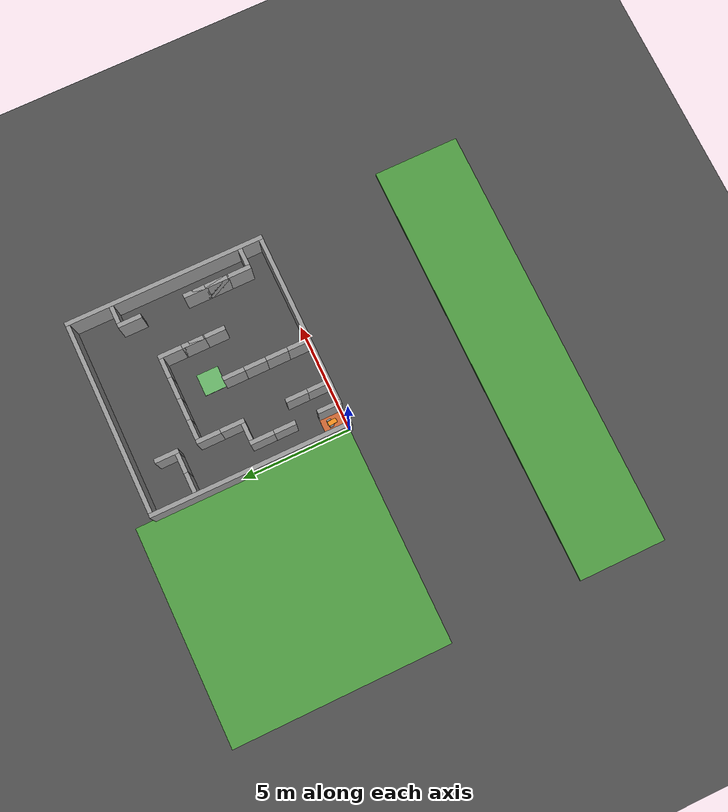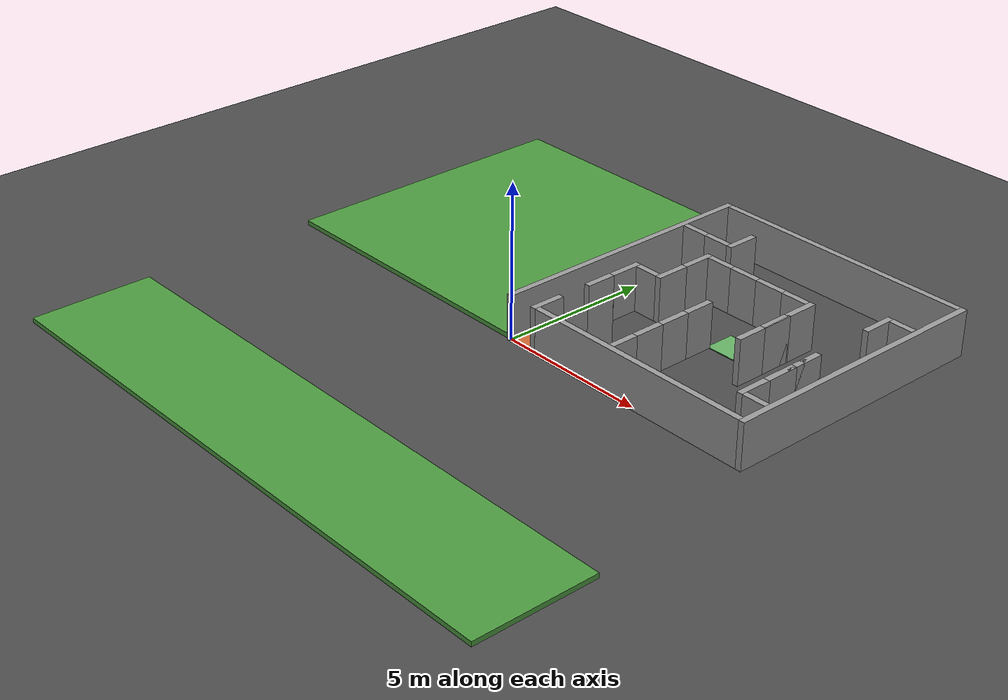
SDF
<sdf version="1.6">
 <world name="default">
  <light name="sun" type="directional">
   <pose>0 0 10 0 -0 0</pose>
   <diffuse>0.8 0.8 0.8 1</diffuse>
   <specular>0.1 0.1 0.1 1</specular>
   <attenuation>
    <range>1000</range>
    <constant>0.9</constant>
    <linear>0.01</linear>
    <quadratic>0.001</quadratic>
   </attenuation>
   <direction>-0.5 0.5 -1</direction>
  </light>
  <model name="ground_plane">
   <static>1</static>
   <link name="link">
    <collision name="collision">
     <geometry><plane><normal>0 0 1</normal><size>20 20</size></plane></geometry>
     <surface><friction><ode><mu>100</mu><mu2>50</mu2></ode></friction></surface>
    </collision>
    <visual name="visual">
     <cast_shadows>0</cast_shadows>
     <geometry><plane><normal>0 0 1</normal><size>20 20</size></plane></geometry>
     <material>
      <script>
       <uri>model://asphalt_plane/materials/scripts</uri>
       <uri>model://asphalt_plane/materials/textures</uri>
       <name>vrc/asphalt</name>
      </script>
     </material>
    </visual>
   </link>
  </model>
  <gravity>0 0 -9.8</gravity>
  <magnetic_field>6e-06 2.3e-05 -4.2e-05</magnetic_field>
  <atmosphere type="adiabatic"/>
  <physics name="default_physics" default="0" type="ode">
   <max_step_size>0.001</max_step_size>
   <real_time_factor>1</real_time_factor>
   <real_time_update_rate>1000</real_time_update_rate>
  </physics>
  <scene><ambient>0.4 0.4 0.4 1</ambient><background>0.7 0.7 0.7 1</background><shadows>1</shadows></scene>
  <spherical_coordinates>
   <surface_model>EARTH_WGS84</surface_model>
   <latitude_deg>0</latitude_deg>
   <longitude_deg>0</longitude_deg>
   <elevation>0</elevation>
   <heading_deg>0</heading_deg>
  </spherical_coordinates>
  <model name="grey_1wall">
   <static>1</static>
   <link name="link">
    <pose>0 0 0.75 0 -0 0</pose>
    <inertial>
     <mass>5</mass>
     <inertia><ixx>1</ixx><ixy>0</ixy><ixz>0</ixz><iyy>1</iyy><iyz>0</iyz><izz>1</izz></inertia>
    </inertial>
    <visual name="ModelPreview_1::link::visual_1">
     <cast_shadows>0</cast_shadows>
     <geometry><box><size>0.9 0.2 1.5</size></box></geometry>
     <material>
      <script>
       <uri>model://grey_wall/materials/scripts</uri>
       <uri>model://grey_wall/materials/textures</uri>
       <name>vrc/grey_wall</name>
      </script>
      <ambient>1 1 1 1</ambient>
      <diffuse>1 1 1 1</diffuse>
      <specular>0 0 0 1</specular>
      <emissive>0 0 0 1</emissive>
      <shader type="vertex"><normal_map>__default__</normal_map></shader>
     </material>
    </visual>
    <collision name="collision">
     <geometry><box><size>0.9 0.2 1.5</size></box></geometry>
     <surface>
      <friction>
       <ode><mu>1</mu><mu2>1</mu2><fdir1>0 0 0</fdir1><slip1>0</slip1><slip2>0</slip2></ode>
       <torsional>
        <coefficient>1</coefficient>
        <patch_radius>0</patch_radius>
        <surface_radius>0</surface_radius>
        <use_patch_radius>1</use_patch_radius>
        <ode><slip>0</slip></ode>
       </torsional>
      </friction>
      <bounce><restitution_coefficient>0</restitution_coefficient><threshold>1e+06</threshold></bounce>
      <contact>
       <collide_without_contact>0</collide_without_contact>
       <collide_without_contact_bitmask>1</collide_without_contact_bitmask>
       <collide_bitmask>1</collide_bitmask>
       <ode>
        <soft_cfm>0</soft_cfm>
        <soft_erp>0.2</soft_erp>
        <kp>1e+13</kp>
        <kd>1</kd>
        <max_vel>0.01</max_vel>
        <min_depth>0</min_depth>
       </ode>
       <bullet>
        <split_impulse>1</split_impulse>
        <split_impulse_penetration_threshold>-0.01</split_impulse_penetration_threshold>
        <soft_cfm>0</soft_cfm>
        <soft_erp>0.2</soft_erp>
        <kp>1e+13</kp>
        <kd>1</kd>
       </bullet>
      </contact>
     </surface>
    </collision>
   </link>
   <static>1</static>
   <pose>2.55 6 0 0 -0 0</pose>
  </model>
  <model name="grey_1wall_0">
   <static>1</static>
   <link name="link">
    <pose>0 0 0.75 0 -0 0</pose>
    <inertial>
     <mass>5</mass>
     <inertia><ixx>1</ixx><ixy>0</ixy><ixz>0</ixz><iyy>1</iyy><iyz>0</iyz><izz>1</izz></inertia>
    </inertial>
    <visual name="ModelPreview_1::link::visual_1">
     <cast_shadows>0</cast_shadows>
     <geometry><box><size>1 0.2 1.5</size></box></geometry>
     <material>
      <script>
       <uri>model://grey_wall/materials/scripts</uri>
       <uri>model://grey_wall/materials/textures</uri>
       <name>vrc/grey_wall</name>
      </script>
      <ambient>1 1 1 1</ambient>
      <diffuse>1 1 1 1</diffuse>
      <specular>0 0 0 1</specular>
      <emissive>0 0 0 1</emissive>
      <shader type="vertex"><normal_map>__default__</normal_map></shader>
     </material>
    </visual>
    <collision name="collision">
     <geometry><box><size>1 0.2 1.5</size></box></geometry>
     <surface>
      <friction>
       <ode><mu>1</mu><mu2>1</mu2><fdir1>0 0 0</fdir1><slip1>0</slip1><slip2>0</slip2></ode>
       <torsional>
        <coefficient>1</coefficient>
        <patch_radius>0</patch_radius>
        <surface_radius>0</surface_radius>
        <use_patch_radius>1</use_patch_radius>
        <ode><slip>0</slip></ode>
       </torsional>
      </friction>
      <bounce><restitution_coefficient>0</restitution_coefficient><threshold>1e+06</threshold></bounce>
      <contact>
       <collide_without_contact>0</collide_without_contact>
       <collide_without_contact_bitmask>1</collide_without_contact_bitmask>
       <collide_bitmask>1</collide_bitmask>
       <ode>
        <soft_cfm>0</soft_cfm>
        <soft_erp>0.2</soft_erp>
        <kp>1e+13</kp>
        <kd>1</kd>
        <max_vel>0.01</max_vel>
        <min_depth>0</min_depth>
       </ode>
       <bullet>
        <split_impulse>1</split_impulse>
        <split_impulse_penetration_threshold>-0.01</split_impulse_penetration_threshold>
        <soft_cfm>0</soft_cfm>
        <soft_erp>0.2</soft_erp>
        <kp>1e+13</kp>
        <kd>1</kd>
       </bullet>
      </contact>
     </surface>
    </collision>
   </link>
   <static>1</static>
   <pose>3.5 6 0 0 -0 0</pose>
  </model>
  <model name="grey_1wall_clone">
   <static>1</static>
   <link name="link">
    <pose>0 0 0.75 0 -0 0</pose>
    <inertial>
     <mass>5</mass>
     <inertia><ixx>1</ixx><ixy>0</ixy><ixz>0</ixz><iyy>1</iyy><iyz>0</iyz><izz>1</izz></inertia>
    </inertial>
    <visual name="ModelPreview_1::link::visual_1">
     <cast_shadows>0</cast_shadows>
     <geometry><box><size>1 0.2 1.5</size></box></geometry>
     <material>
      <script>
       <uri>model://grey_wall/materials/scripts</uri>
       <uri>model://grey_wall/materials/textures</uri>
       <name>vrc/grey_wall</name>
      </script>
      <ambient>1 1 1 1</ambient>
      <diffuse>1 1 1 1</diffuse>
      <specular>0 0 0 1</specular>
      <emissive>0 0 0 1</emissive>
      <shader type="vertex"><normal_map>__default__</normal_map></shader>
     </material>
    </visual>
    <collision name="collision">
     <geometry><box><size>1 0.2 1.5</size></box></geometry>
     <surface>
      <friction>
       <ode><mu>1</mu><mu2>1</mu2><fdir1>0 0 0</fdir1><slip1>0</slip1><slip2>0</slip2></ode>
       <torsional>
        <coefficient>1</coefficient>
        <patch_radius>0</patch_radius>
        <surface_radius>0</surface_radius>
        <use_patch_radius>1</use_patch_radius>
        <ode><slip>0</slip></ode>
       </torsional>
      </friction>
      <bounce><restitution_coefficient>0</restitution_coefficient><threshold>1e+06</threshold></bounce>
      <contact>
       <collide_without_contact>0</collide_without_contact>
       <collide_without_contact_bitmask>1</collide_without_contact_bitmask>
       <collide_bitmask>1</collide_bitmask>
       <ode>
        <soft_cfm>0</soft_cfm>
        <soft_erp>0.2</soft_erp>
        <kp>1e+13</kp>
        <kd>1</kd>
        <max_vel>0.01</max_vel>
        <min_depth>0</min_depth>
       </ode>
       <bullet>
        <split_impulse>1</split_impulse>
        <split_impulse_penetration_threshold>-0.01</split_impulse_penetration_threshold>
        <soft_cfm>0</soft_cfm>
        <soft_erp>0.2</soft_erp>
        <kp>1e+13</kp>
        <kd>1</kd>
       </bullet>
      </contact>
     </surface>
    </collision>
   </link>
   <static>1</static>
   <pose>4.5 6 0 0 -0 0</pose>
  </model>
  <model name="grey_9wall">
   <static>1</static>
   <link name="link">
    <pose>0 0 0.75 0 -0 1.57</pose>
    <inertial>
     <mass>20</mass>
     <inertia><ixx>1</ixx><ixy>0</ixy><ixz>0</ixz><iyy>1</iyy><iyz>0</iyz><izz>1</izz></inertia>
    </inertial>
    <visual name="ModelPreview_1::link::visual_1">
     <cast_shadows>0</cast_shadows>
     <geometry><box><size>9.2 0.2 1.5</size></box></geometry>
     <material>
      <script>
       <uri>model://grey_wall/materials/scripts</uri>
       <uri>model://grey_wall/materials/textures</uri>
       <name>vrc/grey_wall</name>
      </script>
      <ambient>1 1 1 1</ambient>
      <diffuse>1 1 1 1</diffuse>
      <specular>0 0 0 1</specular>
      <emissive>0 0 0 1</emissive>
      <shader type="vertex"><normal_map>__default__</normal_map></shader>
     </material>
    </visual>
    <collision name="collision">
     <geometry><box><size>9.2 0.2 1.5</size></box></geometry>
     <surface>
      <friction>
       <ode><mu>1</mu><mu2>1</mu2><fdir1>0 0 0</fdir1><slip1>0</slip1><slip2>0</slip2></ode>
       <torsional>
        <coefficient>1</coefficient>
        <patch_radius>0</patch_radius>
        <surface_radius>0</surface_radius>
        <use_patch_radius>1</use_patch_radius>
        <ode><slip>0</slip></ode>
       </torsional>
      </friction>
      <bounce><restitution_coefficient>0</restitution_coefficient><threshold>1e+06</threshold></bounce>
      <contact>
       <collide_without_contact>0</collide_without_contact>
       <collide_without_contact_bitmask>1</collide_without_contact_bitmask>
       <collide_bitmask>1</collide_bitmask>
       <ode>
        <soft_cfm>0</soft_cfm>
        <soft_erp>0.2</soft_erp>
        <kp>1e+13</kp>
        <kd>1</kd>
        <max_vel>0.01</max_vel>
        <min_depth>0</min_depth>
       </ode>
       <bullet>
        <split_impulse>1</split_impulse>
        <split_impulse_penetration_threshold>-0.01</split_impulse_penetration_threshold>
        <soft_cfm>0</soft_cfm>
        <soft_erp>0.2</soft_erp>
        <kp>1e+13</kp>
        <kd>1</kd>
       </bullet>
      </contact>
     </surface>
    </collision>
   </link>
   <static>1</static>
   <pose>9 4.5 0 0 -0 0</pose>
  </model>
  <model name="grey_9wall_1">
   <static>1</static>
   <link name="link">
    <pose>0 0 0.75 0 -0 1.57</pose>
    <inertial>
     <mass>20</mass>
     <inertia><ixx>1</ixx><ixy>0</ixy><ixz>0</ixz><iyy>1</iyy><iyz>0</iyz><izz>1</izz></inertia>
    </inertial>
    <visual name="ModelPreview_1::link::visual_1">
     <cast_shadows>0</cast_shadows>
     <geometry><box><size>9.2 0.2 1.5</size></box></geometry>
     <material>
      <script>
       <uri>model://grey_wall/materials/scripts</uri>
       <uri>model://grey_wall/materials/textures</uri>
       <name>vrc/grey_wall</name>
      </script>
      <ambient>1 1 1 1</ambient>
      <diffuse>1 1 1 1</diffuse>
      <specular>0 0 0 1</specular>
      <emissive>0 0 0 1</emissive>
      <shader type="vertex"><normal_map>__default__</normal_map></shader>
     </material>
    </visual>
    <collision name="collision">
     <geometry><box><size>9.2 0.2 1.5</size></box></geometry>
     <surface>
      <friction>
       <ode><mu>1</mu><mu2>1</mu2><fdir1>0 0 0</fdir1><slip1>0</slip1><slip2>0</slip2></ode>
       <torsional>
        <coefficient>1</coefficient>
        <patch_radius>0</patch_radius>
        <surface_radius>0</surface_radius>
        <use_patch_radius>1</use_patch_radius>
        <ode><slip>0</slip></ode>
       </torsional>
      </friction>
      <bounce><restitution_coefficient>0</restitution_coefficient><threshold>1e+06</threshold></bounce>
      <contact>
       <collide_without_contact>0</collide_without_contact>
       <collide_without_contact_bitmask>1</collide_without_contact_bitmask>
       <collide_bitmask>1</collide_bitmask>
       <ode>
        <soft_cfm>0</soft_cfm>
        <soft_erp>0.2</soft_erp>
        <kp>1e+13</kp>
        <kd>1</kd>
        <max_vel>0.01</max_vel>
        <min_depth>0</min_depth>
       </ode>
       <bullet>
        <split_impulse>1</split_impulse>
        <split_impulse_penetration_threshold>-0.01</split_impulse_penetration_threshold>
        <soft_cfm>0</soft_cfm>
        <soft_erp>0.2</soft_erp>
        <kp>1e+13</kp>
        <kd>1</kd>
       </bullet>
      </contact>
     </surface>
    </collision>
   </link>
   <static>1</static>
   <pose>0 4.5 0 0 -0 0</pose>
  </model>
  <model name="grey_9wall_0_0">
   <static>1</static>
   <link name="link">
    <pose>0 0 0.75 0 -0 0</pose>
    <inertial>
     <mass>20</mass>
     <inertia><ixx>1</ixx><ixy>0</ixy><ixz>0</ixz><iyy>1</iyy><iyz>0</iyz><izz>1</izz></inertia>
    </inertial>
    <visual name="ModelPreview_1::link::visual_1">
     <cast_shadows>0</cast_shadows>
     <geometry><box><size>8.8 0.2 1.5</size></box></geometry>
     <material>
      <script>
       <uri>model://grey_wall/materials/scripts</uri>
       <uri>model://grey_wall/materials/textures</uri>
       <name>vrc/grey_wall</name>
      </script>
      <ambient>1 1 1 1</ambient>
      <diffuse>1 1 1 1</diffuse>
      <specular>0 0 0 1</specular>
      <emissive>0 0 0 1</emissive>
      <shader type="vertex"><normal_map>__default__</normal_map></shader>
     </material>
    </visual>
    <collision name="collision">
     <geometry><box><size>8.8 0.2 1.5</size></box></geometry>
     <surface>
      <friction>
       <ode><mu>1</mu><mu2>1</mu2><fdir1>0 0 0</fdir1><slip1>0</slip1><slip2>0</slip2></ode>
       <torsional>
        <coefficient>1</coefficient>
        <patch_radius>0</patch_radius>
        <surface_radius>0</surface_radius>
        <use_patch_radius>1</use_patch_radius>
        <ode><slip>0</slip></ode>
       </torsional>
      </friction>
      <bounce><restitution_coefficient>0</restitution_coefficient><threshold>1e+06</threshold></bounce>
      <contact>
       <collide_without_contact>0</collide_without_contact>
       <collide_without_contact_bitmask>1</collide_without_contact_bitmask>
       <collide_bitmask>1</collide_bitmask>
       <ode>
        <soft_cfm>0</soft_cfm>
        <soft_erp>0.2</soft_erp>
        <kp>1e+13</kp>
        <kd>1</kd>
        <max_vel>0.01</max_vel>
        <min_depth>0</min_depth>
       </ode>
       <bullet>
        <split_impulse>1</split_impulse>
        <split_impulse_penetration_threshold>-0.01</split_impulse_penetration_threshold>
        <soft_cfm>0</soft_cfm>
        <soft_erp>0.2</soft_erp>
        <kp>1e+13</kp>
        <kd>1</kd>
       </bullet>
      </contact>
     </surface>
    </collision>
   </link>
   <static>1</static>
   <pose>4.5 9 0 0 -0 0</pose>
  </model>
  <model name="grey_8wall_2">
   <static>1</static>
   <link name="link">
    <pose>0 0 0.75 0 -0 0</pose>
    <inertial>
     <mass>20</mass>
     <inertia><ixx>1</ixx><ixy>0</ixy><ixz>0</ixz><iyy>1</iyy><iyz>0</iyz><izz>1</izz></inertia>
    </inertial>
    <visual name="ModelPreview_1::link::visual_1">
     <cast_shadows>0</cast_shadows>
     <geometry><box><size>7.8 0.2 1.5</size></box></geometry>
     <material>
      <script>
       <uri>model://grey_wall/materials/scripts</uri>
       <uri>model://grey_wall/materials/textures</uri>
       <name>vrc/grey_wall</name>
      </script>
      <ambient>1 1 1 1</ambient>
      <diffuse>1 1 1 1</diffuse>
      <specular>0 0 0 1</specular>
      <emissive>0 0 0 1</emissive>
      <shader type="vertex"><normal_map>__default__</normal_map></shader>
     </material>
    </visual>
    <collision name="collision">
     <geometry><box><size>8 0.2 1.5</size></box></geometry>
     <surface>
      <friction>
       <ode><mu>1</mu><mu2>1</mu2><fdir1>0 0 0</fdir1><slip1>0</slip1><slip2>0</slip2></ode>
       <torsional>
        <coefficient>1</coefficient>
        <patch_radius>0</patch_radius>
        <surface_radius>0</surface_radius>
        <use_patch_radius>1</use_patch_radius>
        <ode><slip>0</slip></ode>
       </torsional>
      </friction>
      <bounce><restitution_coefficient>0</restitution_coefficient><threshold>1e+06</threshold></bounce>
      <contact>
       <collide_without_contact>0</collide_without_contact>
       <collide_without_contact_bitmask>1</collide_without_contact_bitmask>
       <collide_bitmask>1</collide_bitmask>
       <ode>
        <soft_cfm>0</soft_cfm>
        <soft_erp>0.2</soft_erp>
        <kp>1e+13</kp>
        <kd>1</kd>
        <max_vel>0.01</max_vel>
        <min_depth>0</min_depth>
       </ode>
       <bullet>
        <split_impulse>1</split_impulse>
        <split_impulse_penetration_threshold>-0.01</split_impulse_penetration_threshold>
        <soft_cfm>0</soft_cfm>
        <soft_erp>0.2</soft_erp>
        <kp>1e+13</kp>
        <kd>1</kd>
       </bullet>
      </contact>
     </surface>
    </collision>
   </link>
   <static>1</static>
   <pose>5 0 0 0 -0 0</pose>
  </model>
  <model name="box_goal">
   <static>1</static>
   <link name="link">
    <inertial>
     <mass>1</mass>
     <inertia>
      <ixx>0.166667</ixx>
      <ixy>0</ixy>
      <ixz>0</ixz>
      <iyy>0.166667</iyy>
      <iyz>0</iyz>
      <izz>0.166667</izz>
     </inertia>
    </inertial>
    <visual name="visual">
     <geometry><box><size>1 1 0.1</size></box></geometry>
     <material>
      <script><name>Gazebo/Grey</name><uri>file://media/materials/scripts/gazebo.material</uri></script>
      <ambient>0.3 1 0.3 1</ambient>
      <diffuse>0.4 0.7 0.4 1</diffuse>
      <specular>0.01 0.05 0.01 1</specular>
      <emissive>0 0.02 0 1</emissive>
      <shader type="vertex"><normal_map>__default__</normal_map></shader>
     </material>
    </visual>
    <collision name="collision">
     <geometry><box><size>1 1 0.1</size></box></geometry>
     <surface>
      <friction>
       <ode><mu>1</mu><mu2>1</mu2><fdir1>0 0 0</fdir1><slip1>0</slip1><slip2>0</slip2></ode>
       <torsional>
        <coefficient>1</coefficient>
        <patch_radius>0</patch_radius>
        <surface_radius>0</surface_radius>
        <use_patch_radius>1</use_patch_radius>
        <ode><slip>0</slip></ode>
       </torsional>
      </friction>
      <bounce><restitution_coefficient>0</restitution_coefficient><threshold>1e+06</threshold></bounce>
      <contact>
       <collide_without_contact>0</collide_without_contact>
       <collide_without_contact_bitmask>1</collide_without_contact_bitmask>
       <collide_bitmask>1</collide_bitmask>
       <ode>
        <soft_cfm>0</soft_cfm>
        <soft_erp>0.2</soft_erp>
        <kp>1e+13</kp>
        <kd>1</kd>
        <max_vel>0.01</max_vel>
        <min_depth>0</min_depth>
       </ode>
       <bullet>
        <split_impulse>1</split_impulse>
        <split_impulse_penetration_threshold>-0.01</split_impulse_penetration_threshold>
        <soft_cfm>0</soft_cfm>
        <soft_erp>0.2</soft_erp>
        <kp>1e+13</kp>
        <kd>1</kd>
       </bullet>
      </contact>
     </surface>
    </collision>
   </link>
   <static>0</static>
   <pose>4.5 4.5 -0.049 0 -0 0</pose>
  </model>
  <model name="box_init">
   <static>1</static>
   <link name="link">
    <inertial>
     <mass>1</mass>
     <inertia>
      <ixx>0.166667</ixx>
      <ixy>0</ixy>
      <ixz>0</ixz>
      <iyy>0.166667</iyy>
      <iyz>0</iyz>
      <izz>0.166667</izz>
     </inertia>
    </inertial>
    <visual name="visual">
     <geometry><box><size>1 1 0.1</size></box></geometry>
     <material>
      <script><name>Gazebo/Grey</name><uri>file://media/materials/scripts/gazebo.material</uri></script>
      <ambient>1 0.5 0.2 1</ambient>
      <diffuse>0.8 0.4 0.2 1</diffuse>
      <specular>0.05 0.02 0.01 1</specular>
      <emissive>0 0 0 1</emissive>
      <shader type="vertex"><normal_map>__default__</normal_map></shader>
     </material>
    </visual>
    <collision name="collision">
     <geometry><box><size>1 1 0.1</size></box></geometry>
     <surface>
      <friction>
       <ode><mu>1</mu><mu2>1</mu2><fdir1>0 0 0</fdir1><slip1>0</slip1><slip2>0</slip2></ode>
       <torsional>
        <coefficient>1</coefficient>
        <patch_radius>0</patch_radius>
        <surface_radius>0</surface_radius>
        <use_patch_radius>1</use_patch_radius>
        <ode><slip>0</slip></ode>
       </torsional>
      </friction>
      <bounce><restitution_coefficient>0</restitution_coefficient><threshold>1e+06</threshold></bounce>
      <contact>
       <collide_without_contact>0</collide_without_contact>
       <collide_without_contact_bitmask>1</collide_without_contact_bitmask>
       <collide_bitmask>1</collide_bitmask>
       <ode>
        <soft_cfm>0</soft_cfm>
        <soft_erp>0.2</soft_erp>
        <kp>1e+13</kp>
        <kd>1</kd>
        <max_vel>0.01</max_vel>
        <min_depth>0</min_depth>
       </ode>
       <bullet>
        <split_impulse>1</split_impulse>
        <split_impulse_penetration_threshold>-0.01</split_impulse_penetration_threshold>
        <soft_cfm>0</soft_cfm>
        <soft_erp>0.2</soft_erp>
        <kp>1e+13</kp>
        <kd>1</kd>
       </bullet>
      </contact>
     </surface>
    </collision>
   </link>
   <static>0</static>
   <allow_auto_disable>0</allow_auto_disable>
   <pose>0.5 0.5 -0.049 0 -0 0</pose>
  </model>
  <model name="unit_box_platform">
   <static>1</static>
   <link name="link">
    <pose>9.4118 -2.75754 0 0 -0 0</pose>
    <inertial>
     <mass>10</mass>
     <inertia>
      <ixx>0.166667</ixx>
      <ixy>0</ixy>
      <ixz>0</ixz>
      <iyy>0.166667</iyy>
      <iyz>0</iyz>
      <izz>0.166667</izz>
     </inertia>
    </inertial>
    <visual name="visual">
     <cast_shadows>0</cast_shadows>
     <geometry><box><size>20 4 0.25</size></box></geometry>
     <material>
      <script><name>Gazebo/Grass</name><uri>file://media/materials/textures/gazebo.material</uri></script>
      <ambient>0.3 0.3 0.3 1</ambient>
      <diffuse>0.7 0.7 0.7 1</diffuse>
      <specular>0.01 0.01 0.01 1</specular>
      <emissive>0 0 0 1</emissive>
      <shader type="vertex"><normal_map>__default__</normal_map></shader>
     </material>
     <cast_shadows>0</cast_shadows>
    </visual>
    <collision name="collision">
     <geometry><box><size>20 4 0.25</size></box></geometry>
     <surface>
      <friction>
       <ode><mu>1</mu><mu2>1</mu2><fdir1>0 0 0</fdir1><slip1>0</slip1><slip2>0</slip2></ode>
       <torsional>
        <coefficient>1</coefficient>
        <patch_radius>0</patch_radius>
        <surface_radius>0</surface_radius>
        <use_patch_radius>1</use_patch_radius>
        <ode><slip>0</slip></ode>
       </torsional>
      </friction>
      <bounce><restitution_coefficient>0</restitution_coefficient><threshold>1e+06</threshold></bounce>
      <contact>
       <collide_without_contact>0</collide_without_contact>
       <collide_without_contact_bitmask>1</collide_without_contact_bitmask>
       <collide_bitmask>1</collide_bitmask>
       <ode>
        <soft_cfm>0</soft_cfm>
        <soft_erp>0.2</soft_erp>
        <kp>1e+13</kp>
        <kd>1</kd>
        <max_vel>0.01</max_vel>
        <min_depth>0</min_depth>
       </ode>
       <bullet>
        <split_impulse>1</split_impulse>
        <split_impulse_penetration_threshold>-0.01</split_impulse_penetration_threshold>
        <soft_cfm>0</soft_cfm>
        <soft_erp>0.2</soft_erp>
        <kp>1e+13</kp>
        <kd>1</kd>
       </bullet>
      </contact>
     </surface>
    </collision>
   </link>
   <static>0</static>
   <pose>-9.4118 -5.24246 0.001 0 -0 0</pose>
  </model>
  <model name="unit_box_lawn">
   <static>1</static>
   <link name="link">
    <pose>14.3617 -5.74416 0 0 -0 0</pose>
    <inertial>
     <mass>10</mass>
     <inertia>
      <ixx>0.166667</ixx>
      <ixy>0</ixy>
      <ixz>0</ixz>
      <iyy>0.166667</iyy>
      <iyz>0</iyz>
      <izz>0.166667</izz>
     </inertia>
    </inertial>
    <visual name="visual">
     <geometry><box><size>10 10 0.25</size></box></geometry>
     <material>
      <script><name>Gazebo/Grass</name><uri>file://media/materials/textures/gazebo.material</uri></script>
      <ambient>0.3 0.3 0.3 1</ambient>
      <diffuse>0.7 0.7 0.7 1</diffuse>
      <specular>0.01 0.01 0.01 1</specular>
      <emissive>0 0 0 1</emissive>
      <shader type="vertex"><normal_map>__default__</normal_map></shader>
     </material>
    </visual>
    <collision name="collision">
     <geometry><box><size>10 10 0.25</size></box></geometry>
     <surface>
      <friction>
       <ode><mu>1</mu><mu2>1</mu2><fdir1>0 0 0</fdir1><slip1>0</slip1><slip2>0</slip2></ode>
       <torsional>
        <coefficient>1</coefficient>
        <patch_radius>0</patch_radius>
        <surface_radius>0</surface_radius>
        <use_patch_radius>1</use_patch_radius>
        <ode><slip>0</slip></ode>
       </torsional>
      </friction>
      <bounce><restitution_coefficient>0</restitution_coefficient><threshold>1e+06</threshold></bounce>
      <contact>
       <collide_without_contact>0</collide_without_contact>
       <collide_without_contact_bitmask>1</collide_without_contact_bitmask>
       <collide_bitmask>1</collide_bitmask>
       <ode>
        <soft_cfm>0</soft_cfm>
        <soft_erp>0.2</soft_erp>
        <kp>1e+13</kp>
        <kd>1</kd>
        <max_vel>0.01</max_vel>
        <min_depth>0</min_depth>
       </ode>
       <bullet>
        <split_impulse>1</split_impulse>
        <split_impulse_penetration_threshold>-0.01</split_impulse_penetration_threshold>
        <soft_cfm>0</soft_cfm>
        <soft_erp>0.2</soft_erp>
        <kp>1e+13</kp>
        <kd>1</kd>
       </bullet>
      </contact>
     </surface>
    </collision>
   </link>
   <static>0</static>
   <pose>-19.3617 10.7442 0.001 0 -0 0</pose>
  </model>
  <model name="grey_1wall_clone_0">
   <static>1</static>
   <link name="link">
    <pose>0 0 0.75 0 -0 0</pose>
    <inertial>
     <mass>5</mass>
     <inertia><ixx>1</ixx><ixy>0</ixy><ixz>0</ixz><iyy>1</iyy><iyz>0</iyz><izz>1</izz></inertia>
    </inertial>
    <visual name="ModelPreview_1::link::visual_1">
     <cast_shadows>0</cast_shadows>
     <geometry><box><size>0.9 0.2 1.5</size></box></geometry>
     <material>
      <script>
       <uri>model://grey_wall/materials/scripts</uri>
       <uri>model://grey_wall/materials/textures</uri>
       <name>vrc/grey_wall</name>
      </script>
      <ambient>1 1 1 1</ambient>
      <diffuse>1 1 1 1</diffuse>
      <specular>0 0 0 1</specular>
      <emissive>0 0 0 1</emissive>
      <shader type="vertex"><normal_map>__default__</normal_map></shader>
     </material>
    </visual>
    <collision name="collision">
     <geometry><box><size>0.9 0.2 1.5</size></box></geometry>
     <surface>
      <friction>
       <ode><mu>1</mu><mu2>1</mu2><fdir1>0 0 0</fdir1><slip1>0</slip1><slip2>0</slip2></ode>
       <torsional>
        <coefficient>1</coefficient>
        <patch_radius>0</patch_radius>
        <surface_radius>0</surface_radius>
        <use_patch_radius>1</use_patch_radius>
        <ode><slip>0</slip></ode>
       </torsional>
      </friction>
      <bounce><restitution_coefficient>0</restitution_coefficient><threshold>1e+06</threshold></bounce>
      <contact>
       <collide_without_contact>0</collide_without_contact>
       <collide_without_contact_bitmask>1</collide_without_contact_bitmask>
       <collide_bitmask>1</collide_bitmask>
       <ode>
        <soft_cfm>0</soft_cfm>
        <soft_erp>0.2</soft_erp>
        <kp>1e+13</kp>
        <kd>1</kd>
        <max_vel>0.01</max_vel>
        <min_depth>0</min_depth>
       </ode>
       <bullet>
        <split_impulse>1</split_impulse>
        <split_impulse_penetration_threshold>-0.01</split_impulse_penetration_threshold>
        <soft_cfm>0</soft_cfm>
        <soft_erp>0.2</soft_erp>
        <kp>1e+13</kp>
        <kd>1</kd>
       </bullet>
      </contact>
     </surface>
    </collision>
   </link>
   <static>1</static>
   <pose>0.55 7 0 0 -0 0</pose>
  </model>
  <model name="grey_1wall_clone_1">
   <static>1</static>
   <link name="link">
    <pose>0 0 0.75 0 -0 0</pose>
    <inertial>
     <mass>5</mass>
     <inertia><ixx>1</ixx><ixy>0</ixy><ixz>0</ixz><iyy>1</iyy><iyz>0</iyz><izz>1</izz></inertia>
    </inertial>
    <visual name="ModelPreview_1::link::visual_1">
     <cast_shadows>0</cast_shadows>
     <geometry><box><size>0.9 0.2 1.5</size></box></geometry>
     <material>
      <script>
       <uri>model://grey_wall/materials/scripts</uri>
       <uri>model://grey_wall/materials/textures</uri>
       <name>vrc/grey_wall</name>
      </script>
      <ambient>1 1 1 1</ambient>
      <diffuse>1 1 1 1</diffuse>
      <specular>0 0 0 1</specular>
      <emissive>0 0 0 1</emissive>
      <shader type="vertex"><normal_map>__default__</normal_map></shader>
     </material>
    </visual>
    <collision name="collision">
     <geometry><box><size>0.9 0.2 1.5</size></box></geometry>
     <surface>
      <friction>
       <ode><mu>1</mu><mu2>1</mu2><fdir1>0 0 0</fdir1><slip1>0</slip1><slip2>0</slip2></ode>
       <torsional>
        <coefficient>1</coefficient>
        <patch_radius>0</patch_radius>
        <surface_radius>0</surface_radius>
        <use_patch_radius>1</use_patch_radius>
        <ode><slip>0</slip></ode>
       </torsional>
      </friction>
      <bounce><restitution_coefficient>0</restitution_coefficient><threshold>1e+06</threshold></bounce>
      <contact>
       <collide_without_contact>0</collide_without_contact>
       <collide_without_contact_bitmask>1</collide_without_contact_bitmask>
       <collide_bitmask>1</collide_bitmask>
       <ode>
        <soft_cfm>0</soft_cfm>
        <soft_erp>0.2</soft_erp>
        <kp>1e+13</kp>
        <kd>1</kd>
        <max_vel>0.01</max_vel>
        <min_depth>0</min_depth>
       </ode>
       <bullet>
        <split_impulse>1</split_impulse>
        <split_impulse_penetration_threshold>-0.01</split_impulse_penetration_threshold>
        <soft_cfm>0</soft_cfm>
        <soft_erp>0.2</soft_erp>
        <kp>1e+13</kp>
        <kd>1</kd>
       </bullet>
      </contact>
     </surface>
    </collision>
   </link>
   <static>1</static>
   <pose>1.45 7 0 0 -0 0</pose>
  </model>
  <model name="grey_1wall_90">
   <static>1</static>
   <link name="link">
    <pose>0 0 0.75 0 -0 0</pose>
    <inertial>
     <mass>5</mass>
     <inertia><ixx>1</ixx><ixy>0</ixy><ixz>0</ixz><iyy>1</iyy><iyz>0</iyz><izz>1</izz></inertia>
    </inertial>
    <visual name="ModelPreview_1::link::visual_1">
     <cast_shadows>0</cast_shadows>
     <geometry><box><size>1.1 0.2 1.5</size></box></geometry>
     <material>
      <script>
       <uri>model://grey_wall/materials/scripts</uri>
       <uri>model://grey_wall/materials/textures</uri>
       <name>vrc/grey_wall</name>
      </script>
      <ambient>1 1 1 1</ambient>
      <diffuse>1 1 1 1</diffuse>
      <specular>0 0 0 1</specular>
      <emissive>0 0 0 1</emissive>
      <shader type="vertex"><normal_map>__default__</normal_map></shader>
     </material>
    </visual>
    <collision name="collision">
     <geometry><box><size>1.1 0.2 1.5</size></box></geometry>
     <surface>
      <friction>
       <ode><mu>1</mu><mu2>1</mu2><fdir1>0 0 0</fdir1><slip1>0</slip1><slip2>0</slip2></ode>
       <torsional>
        <coefficient>1</coefficient>
        <patch_radius>0</patch_radius>
        <surface_radius>0</surface_radius>
        <use_patch_radius>1</use_patch_radius>
        <ode><slip>0</slip></ode>
       </torsional>
      </friction>
      <bounce><restitution_coefficient>0</restitution_coefficient><threshold>1e+06</threshold></bounce>
      <contact>
       <collide_without_contact>0</collide_without_contact>
       <collide_without_contact_bitmask>1</collide_without_contact_bitmask>
       <collide_bitmask>1</collide_bitmask>
       <ode>
        <soft_cfm>0</soft_cfm>
        <soft_erp>0.2</soft_erp>
        <kp>1e+13</kp>
        <kd>1</kd>
        <max_vel>0.01</max_vel>
        <min_depth>0</min_depth>
       </ode>
       <bullet>
        <split_impulse>1</split_impulse>
        <split_impulse_penetration_threshold>-0.01</split_impulse_penetration_threshold>
        <soft_cfm>0</soft_cfm>
        <soft_erp>0.2</soft_erp>
        <kp>1e+13</kp>
        <kd>1</kd>
       </bullet>
      </contact>
     </surface>
    </collision>
   </link>
   <static>1</static>
   <pose>2 7.45 0 0 -0 1.57</pose>
  </model>
  <model name="grey_1wall_0_clone">
   <static>1</static>
   <link name="link">
    <pose>0 0 0.75 0 -0 0</pose>
    <inertial>
     <mass>5</mass>
     <inertia><ixx>1</ixx><ixy>0</ixy><ixz>0</ixz><iyy>1</iyy><iyz>0</iyz><izz>1</izz></inertia>
    </inertial>
    <visual name="ModelPreview_1::link::visual_1">
     <cast_shadows>0</cast_shadows>
     <geometry><box><size>0.9 0.2 1.5</size></box></geometry>
     <material>
      <script>
       <uri>model://grey_wall/materials/scripts</uri>
       <uri>model://grey_wall/materials/textures</uri>
       <name>vrc/grey_wall</name>
      </script>
      <ambient>1 1 1 1</ambient>
      <diffuse>1 1 1 1</diffuse>
      <specular>0 0 0 1</specular>
      <emissive>0 0 0 1</emissive>
      <shader type="vertex"><normal_map>__default__</normal_map></shader>
     </material>
    </visual>
    <collision name="collision">
     <geometry><box><size>0.9 0.2 1.5</size></box></geometry>
     <surface>
      <friction>
       <ode><mu>1</mu><mu2>1</mu2><fdir1>0 0 0</fdir1><slip1>0</slip1><slip2>0</slip2></ode>
       <torsional>
        <coefficient>1</coefficient>
        <patch_radius>0</patch_radius>
        <surface_radius>0</surface_radius>
        <use_patch_radius>1</use_patch_radius>
        <ode><slip>0</slip></ode>
       </torsional>
      </friction>
      <bounce><restitution_coefficient>0</restitution_coefficient><threshold>1e+06</threshold></bounce>
      <contact>
       <collide_without_contact>0</collide_without_contact>
       <collide_without_contact_bitmask>1</collide_without_contact_bitmask>
       <collide_bitmask>1</collide_bitmask>
       <ode>
        <soft_cfm>0</soft_cfm>
        <soft_erp>0.2</soft_erp>
        <kp>1e+13</kp>
        <kd>1</kd>
        <max_vel>0.01</max_vel>
        <min_depth>0</min_depth>
       </ode>
       <bullet>
        <split_impulse>1</split_impulse>
        <split_impulse_penetration_threshold>-0.01</split_impulse_penetration_threshold>
        <soft_cfm>0</soft_cfm>
        <soft_erp>0.2</soft_erp>
        <kp>1e+13</kp>
        <kd>1</kd>
       </bullet>
      </contact>
     </surface>
    </collision>
   </link>
   <static>1</static>
   <pose>5.45 6 0 0 -0 0</pose>
  </model>
  <model name="grey_1wall_90_clone">
   <static>1</static>
   <link name="link">
    <pose>0 0 0.75 0 -0 0</pose>
    <inertial>
     <mass>5</mass>
     <inertia><ixx>1</ixx><ixy>0</ixy><ixz>0</ixz><iyy>1</iyy><iyz>0</iyz><izz>1</izz></inertia>
    </inertial>
    <visual name="ModelPreview_1::link::visual_1">
     <cast_shadows>0</cast_shadows>
     <geometry><box><size>1.1 0.2 1.5</size></box></geometry>
     <material>
      <script>
       <uri>model://grey_wall/materials/scripts</uri>
       <uri>model://grey_wall/materials/textures</uri>
       <name>vrc/grey_wall</name>
      </script>
      <ambient>1 1 1 1</ambient>
      <diffuse>1 1 1 1</diffuse>
      <specular>0 0 0 1</specular>
      <emissive>0 0 0 1</emissive>
      <shader type="vertex"><normal_map>__default__</normal_map></shader>
     </material>
    </visual>
    <collision name="collision">
     <geometry><box><size>1.1 0.2 1.5</size></box></geometry>
     <surface>
      <friction>
       <ode><mu>1</mu><mu2>1</mu2><fdir1>0 0 0</fdir1><slip1>0</slip1><slip2>0</slip2></ode>
       <torsional>
        <coefficient>1</coefficient>
        <patch_radius>0</patch_radius>
        <surface_radius>0</surface_radius>
        <use_patch_radius>1</use_patch_radius>
        <ode><slip>0</slip></ode>
       </torsional>
      </friction>
      <bounce><restitution_coefficient>0</restitution_coefficient><threshold>1e+06</threshold></bounce>
      <contact>
       <collide_without_contact>0</collide_without_contact>
       <collide_without_contact_bitmask>1</collide_without_contact_bitmask>
       <collide_bitmask>1</collide_bitmask>
       <ode>
        <soft_cfm>0</soft_cfm>
        <soft_erp>0.2</soft_erp>
        <kp>1e+13</kp>
        <kd>1</kd>
        <max_vel>0.01</max_vel>
        <min_depth>0</min_depth>
       </ode>
       <bullet>
        <split_impulse>1</split_impulse>
        <split_impulse_penetration_threshold>-0.01</split_impulse_penetration_threshold>
        <soft_cfm>0</soft_cfm>
        <soft_erp>0.2</soft_erp>
        <kp>1e+13</kp>
        <kd>1</kd>
       </bullet>
      </contact>
     </surface>
    </collision>
   </link>
   <static>1</static>
   <pose>2 5.55 0 0 -0 1.57</pose>
  </model>
  <model name="grey_1wall_90_clone_0">
   <static>1</static>
   <link name="link">
    <pose>0 0 0.75 0 -0 0</pose>
    <inertial>
     <mass>5</mass>
     <inertia><ixx>1</ixx><ixy>0</ixy><ixz>0</ixz><iyy>1</iyy><iyz>0</iyz><izz>1</izz></inertia>
    </inertial>
    <visual name="ModelPreview_1::link::visual_1">
     <cast_shadows>0</cast_shadows>
     <geometry><box><size>1.1 0.2 1.5</size></box></geometry>
     <material>
      <script>
       <uri>model://grey_wall/materials/scripts</uri>
       <uri>model://grey_wall/materials/textures</uri>
       <name>vrc/grey_wall</name>
      </script>
      <ambient>1 1 1 1</ambient>
      <diffuse>1 1 1 1</diffuse>
      <specular>0 0 0 1</specular>
      <emissive>0 0 0 1</emissive>
      <shader type="vertex"><normal_map>__default__</normal_map></shader>
     </material>
    </visual>
    <collision name="collision">
     <geometry><box><size>1.1 0.2 1.5</size></box></geometry>
     <surface>
      <friction>
       <ode><mu>1</mu><mu2>1</mu2><fdir1>0 0 0</fdir1><slip1>0</slip1><slip2>0</slip2></ode>
       <torsional>
        <coefficient>1</coefficient>
        <patch_radius>0</patch_radius>
        <surface_radius>0</surface_radius>
        <use_patch_radius>1</use_patch_radius>
        <ode><slip>0</slip></ode>
       </torsional>
      </friction>
      <bounce><restitution_coefficient>0</restitution_coefficient><threshold>1e+06</threshold></bounce>
      <contact>
       <collide_without_contact>0</collide_without_contact>
       <collide_without_contact_bitmask>1</collide_without_contact_bitmask>
       <collide_bitmask>1</collide_bitmask>
       <ode>
        <soft_cfm>0</soft_cfm>
        <soft_erp>0.2</soft_erp>
        <kp>1e+13</kp>
        <kd>1</kd>
        <max_vel>0.01</max_vel>
        <min_depth>0</min_depth>
       </ode>
       <bullet>
        <split_impulse>1</split_impulse>
        <split_impulse_penetration_threshold>-0.01</split_impulse_penetration_threshold>
        <soft_cfm>0</soft_cfm>
        <soft_erp>0.2</soft_erp>
        <kp>1e+13</kp>
        <kd>1</kd>
       </bullet>
      </contact>
     </surface>
    </collision>
   </link>
   <static>1</static>
   <pose>2 4.45 0 0 -0 1.57</pose>
  </model>
  <model name="grey_1wall_90_clone_1">
   <static>1</static>
   <link name="link">
    <pose>0 0 0.75 0 -0 0</pose>
    <inertial>
     <mass>5</mass>
     <inertia><ixx>1</ixx><ixy>0</ixy><ixz>0</ixz><iyy>1</iyy><iyz>0</iyz><izz>1</izz></inertia>
    </inertial>
    <visual name="ModelPreview_1::link::visual_1">
     <cast_shadows>0</cast_shadows>
     <geometry><box><size>1 0.2 1.5</size></box></geometry>
     <material>
      <script>
       <uri>model://grey_wall/materials/scripts</uri>
       <uri>model://grey_wall/materials/textures</uri>
       <name>vrc/grey_wall</name>
      </script>
      <ambient>1 1 1 1</ambient>
      <diffuse>1 1 1 1</diffuse>
      <specular>0 0 0 1</specular>
      <emissive>0 0 0 1</emissive>
      <shader type="vertex"><normal_map>__default__</normal_map></shader>
     </material>
    </visual>
    <collision name="collision">
     <geometry><box><size>1 0.2 1.5</size></box></geometry>
     <surface>
      <friction>
       <ode><mu>1</mu><mu2>1</mu2><fdir1>0 0 0</fdir1><slip1>0</slip1><slip2>0</slip2></ode>
       <torsional>
        <coefficient>1</coefficient>
        <patch_radius>0</patch_radius>
        <surface_radius>0</surface_radius>
        <use_patch_radius>1</use_patch_radius>
        <ode><slip>0</slip></ode>
       </torsional>
      </friction>
      <bounce><restitution_coefficient>0</restitution_coefficient><threshold>1e+06</threshold></bounce>
      <contact>
       <collide_without_contact>0</collide_without_contact>
       <collide_without_contact_bitmask>1</collide_without_contact_bitmask>
       <collide_bitmask>1</collide_bitmask>
       <ode>
        <soft_cfm>0</soft_cfm>
        <soft_erp>0.2</soft_erp>
        <kp>1e+13</kp>
        <kd>1</kd>
        <max_vel>0.01</max_vel>
        <min_depth>0</min_depth>
       </ode>
       <bullet>
        <split_impulse>1</split_impulse>
        <split_impulse_penetration_threshold>-0.01</split_impulse_penetration_threshold>
        <soft_cfm>0</soft_cfm>
        <soft_erp>0.2</soft_erp>
        <kp>1e+13</kp>
        <kd>1</kd>
       </bullet>
      </contact>
     </surface>
    </collision>
   </link>
   <static>1</static>
   <pose>1 2.5 0 0 -0 1.57</pose>
  </model>
  <model name="grey_1wall_90_clone_2">
   <static>1</static>
   <link name="link">
    <pose>0 0 0.75 0 -0 0</pose>
    <inertial>
     <mass>5</mass>
     <inertia><ixx>1</ixx><ixy>0</ixy><ixz>0</ixz><iyy>1</iyy><iyz>0</iyz><izz>1</izz></inertia>
    </inertial>
    <visual name="ModelPreview_1::link::visual_1">
     <cast_shadows>0</cast_shadows>
     <geometry><box><size>1.1 0.2 1.5</size></box></geometry>
     <material>
      <script>
       <uri>model://grey_wall/materials/scripts</uri>
       <uri>model://grey_wall/materials/textures</uri>
       <name>vrc/grey_wall</name>
      </script>
      <ambient>1 1 1 1</ambient>
      <diffuse>1 1 1 1</diffuse>
      <specular>0 0 0 1</specular>
      <emissive>0 0 0 1</emissive>
      <shader type="vertex"><normal_map>__default__</normal_map></shader>
     </material>
    </visual>
    <collision name="collision">
     <geometry><box><size>1.1 0.2 1.5</size></box></geometry>
     <surface>
      <friction>
       <ode><mu>1</mu><mu2>1</mu2><fdir1>0 0 0</fdir1><slip1>0</slip1><slip2>0</slip2></ode>
       <torsional>
        <coefficient>1</coefficient>
        <patch_radius>0</patch_radius>
        <surface_radius>0</surface_radius>
        <use_patch_radius>1</use_patch_radius>
        <ode><slip>0</slip></ode>
       </torsional>
      </friction>
      <bounce><restitution_coefficient>0</restitution_coefficient><threshold>1e+06</threshold></bounce>
      <contact>
       <collide_without_contact>0</collide_without_contact>
       <collide_without_contact_bitmask>1</collide_without_contact_bitmask>
       <collide_bitmask>1</collide_bitmask>
       <ode>
        <soft_cfm>0</soft_cfm>
        <soft_erp>0.2</soft_erp>
        <kp>1e+13</kp>
        <kd>1</kd>
        <max_vel>0.01</max_vel>
        <min_depth>0</min_depth>
       </ode>
       <bullet>
        <split_impulse>1</split_impulse>
        <split_impulse_penetration_threshold>-0.01</split_impulse_penetration_threshold>
        <soft_cfm>0</soft_cfm>
        <soft_erp>0.2</soft_erp>
        <kp>1e+13</kp>
        <kd>1</kd>
       </bullet>
      </contact>
     </surface>
    </collision>
   </link>
   <static>1</static>
   <pose>1 3.55 0 0 -0 1.57</pose>
  </model>
  <model name="grey_1wall_90_clone_3">
   <static>1</static>
   <link name="link">
    <pose>0 0 0.75 0 -0 0</pose>
    <inertial>
     <mass>5</mass>
     <inertia><ixx>1</ixx><ixy>0</ixy><ixz>0</ixz><iyy>1</iyy><iyz>0</iyz><izz>1</izz></inertia>
    </inertial>
    <visual name="ModelPreview_1::link::visual_1">
     <cast_shadows>0</cast_shadows>
     <geometry><box><size>1.1 0.2 1.5</size></box></geometry>
     <material>
      <script>
       <uri>model://grey_wall/materials/scripts</uri>
       <uri>model://grey_wall/materials/textures</uri>
       <name>vrc/grey_wall</name>
      </script>
      <ambient>1 1 1 1</ambient>
      <diffuse>1 1 1 1</diffuse>
      <specular>0 0 0 1</specular>
      <emissive>0 0 0 1</emissive>
      <shader type="vertex"><normal_map>__default__</normal_map></shader>
     </material>
    </visual>
    <collision name="collision">
     <geometry><box><size>1.1 0.2 1.5</size></box></geometry>
     <surface>
      <friction>
       <ode><mu>1</mu><mu2>1</mu2><fdir1>0 0 0</fdir1><slip1>0</slip1><slip2>0</slip2></ode>
       <torsional>
        <coefficient>1</coefficient>
        <patch_radius>0</patch_radius>
        <surface_radius>0</surface_radius>
        <use_patch_radius>1</use_patch_radius>
        <ode><slip>0</slip></ode>
       </torsional>
      </friction>
      <bounce><restitution_coefficient>0</restitution_coefficient><threshold>1e+06</threshold></bounce>
      <contact>
       <collide_without_contact>0</collide_without_contact>
       <collide_without_contact_bitmask>1</collide_without_contact_bitmask>
       <collide_bitmask>1</collide_bitmask>
       <ode>
        <soft_cfm>0</soft_cfm>
        <soft_erp>0.2</soft_erp>
        <kp>1e+13</kp>
        <kd>1</kd>
        <max_vel>0.01</max_vel>
        <min_depth>0</min_depth>
       </ode>
       <bullet>
        <split_impulse>1</split_impulse>
        <split_impulse_penetration_threshold>-0.01</split_impulse_penetration_threshold>
        <soft_cfm>0</soft_cfm>
        <soft_erp>0.2</soft_erp>
        <kp>1e+13</kp>
        <kd>1</kd>
       </bullet>
      </contact>
     </surface>
    </collision>
   </link>
   <static>1</static>
   <pose>1 0.45 0 0 -0 1.57</pose>
  </model>
  <model name="grey_1wall_90_clone_2_clone">
   <static>1</static>
   <link name="link">
    <pose>0 0 0.75 0 -0 0</pose>
    <inertial>
     <mass>5</mass>
     <inertia><ixx>1</ixx><ixy>0</ixy><ixz>0</ixz><iyy>1</iyy><iyz>0</iyz><izz>1</izz></inertia>
    </inertial>
    <visual name="ModelPreview_1::link::visual_1">
     <cast_shadows>0</cast_shadows>
     <geometry><box><size>0.9 0.2 1.5</size></box></geometry>
     <material>
      <script>
       <uri>model://grey_wall/materials/scripts</uri>
       <uri>model://grey_wall/materials/textures</uri>
       <name>vrc/grey_wall</name>
      </script>
      <ambient>1 1 1 1</ambient>
      <diffuse>1 1 1 1</diffuse>
      <specular>0 0 0 1</specular>
      <emissive>0 0 0 1</emissive>
      <shader type="vertex"><normal_map>__default__</normal_map></shader>
     </material>
    </visual>
    <collision name="collision">
     <geometry><box><size>0.9 0.2 1.5</size></box></geometry>
     <surface>
      <friction>
       <ode><mu>1</mu><mu2>1</mu2><fdir1>0 0 0</fdir1><slip1>0</slip1><slip2>0</slip2></ode>
       <torsional>
        <coefficient>1</coefficient>
        <patch_radius>0</patch_radius>
        <surface_radius>0</surface_radius>
        <use_patch_radius>1</use_patch_radius>
        <ode><slip>0</slip></ode>
       </torsional>
      </friction>
      <bounce><restitution_coefficient>0</restitution_coefficient><threshold>1e+06</threshold></bounce>
      <contact>
       <collide_without_contact>0</collide_without_contact>
       <collide_without_contact_bitmask>1</collide_without_contact_bitmask>
       <collide_bitmask>1</collide_bitmask>
       <ode>
        <soft_cfm>0</soft_cfm>
        <soft_erp>0.2</soft_erp>
        <kp>1e+13</kp>
        <kd>1</kd>
        <max_vel>0.01</max_vel>
        <min_depth>0</min_depth>
       </ode>
       <bullet>
        <split_impulse>1</split_impulse>
        <split_impulse_penetration_threshold>-0.01</split_impulse_penetration_threshold>
        <soft_cfm>0</soft_cfm>
        <soft_erp>0.2</soft_erp>
        <kp>1e+13</kp>
        <kd>1</kd>
       </bullet>
      </contact>
     </surface>
    </collision>
   </link>
   <static>1</static>
   <pose>2 0.55 0 0 -0 1.57</pose>
  </model>
  <model name="grey_1wall_90_clone_2_clone_0">
   <static>1</static>
   <link name="link">
    <pose>0 0 0.75 0 -0 0</pose>
    <inertial>
     <mass>5</mass>
     <inertia><ixx>1</ixx><ixy>0</ixy><ixz>0</ixz><iyy>1</iyy><iyz>0</iyz><izz>1</izz></inertia>
    </inertial>
    <visual name="ModelPreview_1::link::visual_1">
     <cast_shadows>0</cast_shadows>
     <geometry><box><size>1 0.2 1.5</size></box></geometry>
     <material>
      <script>
       <uri>model://grey_wall/materials/scripts</uri>
       <uri>model://grey_wall/materials/textures</uri>
       <name>vrc/grey_wall</name>
      </script>
      <ambient>1 1 1 1</ambient>
      <diffuse>1 1 1 1</diffuse>
      <specular>0 0 0 1</specular>
      <emissive>0 0 0 1</emissive>
      <shader type="vertex"><normal_map>__default__</normal_map></shader>
     </material>
    </visual>
    <collision name="collision">
     <geometry><box><size>1 0.2 1.5</size></box></geometry>
     <surface>
      <friction>
       <ode><mu>1</mu><mu2>1</mu2><fdir1>0 0 0</fdir1><slip1>0</slip1><slip2>0</slip2></ode>
       <torsional>
        <coefficient>1</coefficient>
        <patch_radius>0</patch_radius>
        <surface_radius>0</surface_radius>
        <use_patch_radius>1</use_patch_radius>
        <ode><slip>0</slip></ode>
       </torsional>
      </friction>
      <bounce><restitution_coefficient>0</restitution_coefficient><threshold>1e+06</threshold></bounce>
      <contact>
       <collide_without_contact>0</collide_without_contact>
       <collide_without_contact_bitmask>1</collide_without_contact_bitmask>
       <collide_bitmask>1</collide_bitmask>
       <ode>
        <soft_cfm>0</soft_cfm>
        <soft_erp>0.2</soft_erp>
        <kp>1e+13</kp>
        <kd>1</kd>
        <max_vel>0.01</max_vel>
        <min_depth>0</min_depth>
       </ode>
       <bullet>
        <split_impulse>1</split_impulse>
        <split_impulse_penetration_threshold>-0.01</split_impulse_penetration_threshold>
        <soft_cfm>0</soft_cfm>
        <soft_erp>0.2</soft_erp>
        <kp>1e+13</kp>
        <kd>1</kd>
       </bullet>
      </contact>
     </surface>
    </collision>
   </link>
   <static>1</static>
   <pose>2 1.5 0 0 -0 1.57</pose>
  </model>
  <model name="grey_1wall_90_clone_2_clone_1">
   <static>1</static>
   <link name="link">
    <pose>0 0 0.75 0 -0 0</pose>
    <inertial>
     <mass>5</mass>
     <inertia><ixx>1</ixx><ixy>0</ixy><ixz>0</ixz><iyy>1</iyy><iyz>0</iyz><izz>1</izz></inertia>
    </inertial>
    <visual name="ModelPreview_1::link::visual_1">
     <cast_shadows>0</cast_shadows>
     <geometry><box><size>0.9 0.2 1.5</size></box></geometry>
     <material>
      <script>
       <uri>model://grey_wall/materials/scripts</uri>
       <uri>model://grey_wall/materials/textures</uri>
       <name>vrc/grey_wall</name>
      </script>
      <ambient>1 1 1 1</ambient>
      <diffuse>1 1 1 1</diffuse>
      <specular>0 0 0 1</specular>
      <emissive>0 0 0 1</emissive>
      <shader type="vertex"><normal_map>__default__</normal_map></shader>
     </material>
    </visual>
    <collision name="collision">
     <geometry><box><size>0.9 0.2 1.5</size></box></geometry>
     <surface>
      <friction>
       <ode><mu>1</mu><mu2>1</mu2><fdir1>0 0 0</fdir1><slip1>0</slip1><slip2>0</slip2></ode>
       <torsional>
        <coefficient>1</coefficient>
        <patch_radius>0</patch_radius>
        <surface_radius>0</surface_radius>
        <use_patch_radius>1</use_patch_radius>
        <ode><slip>0</slip></ode>
       </torsional>
      </friction>
      <bounce><restitution_coefficient>0</restitution_coefficient><threshold>1e+06</threshold></bounce>
      <contact>
       <collide_without_contact>0</collide_without_contact>
       <collide_without_contact_bitmask>1</collide_without_contact_bitmask>
       <collide_bitmask>1</collide_bitmask>
       <ode>
        <soft_cfm>0</soft_cfm>
        <soft_erp>0.2</soft_erp>
        <kp>1e+13</kp>
        <kd>1</kd>
        <max_vel>0.01</max_vel>
        <min_depth>0</min_depth>
       </ode>
       <bullet>
        <split_impulse>1</split_impulse>
        <split_impulse_penetration_threshold>-0.01</split_impulse_penetration_threshold>
        <soft_cfm>0</soft_cfm>
        <soft_erp>0.2</soft_erp>
        <kp>1e+13</kp>
        <kd>1</kd>
       </bullet>
      </contact>
     </surface>
    </collision>
   </link>
   <static>1</static>
   <pose>4 0.55 0 0 -0 1.57</pose>
  </model>
  <model name="grey_1wall_90_clone_2_clone_2">
   <static>1</static>
   <link name="link">
    <pose>0 0 0.75 0 -0 0</pose>
    <inertial>
     <mass>5</mass>
     <inertia><ixx>1</ixx><ixy>0</ixy><ixz>0</ixz><iyy>1</iyy><iyz>0</iyz><izz>1</izz></inertia>
    </inertial>
    <visual name="ModelPreview_1::link::visual_1">
     <cast_shadows>0</cast_shadows>
     <geometry><box><size>1 0.2 1.5</size></box></geometry>
     <material>
      <script>
       <uri>model://grey_wall/materials/scripts</uri>
       <uri>model://grey_wall/materials/textures</uri>
       <name>vrc/grey_wall</name>
      </script>
      <ambient>1 1 1 1</ambient>
      <diffuse>1 1 1 1</diffuse>
      <specular>0 0 0 1</specular>
      <emissive>0 0 0 1</emissive>
      <shader type="vertex"><normal_map>__default__</normal_map></shader>
     </material>
    </visual>
    <collision name="collision">
     <geometry><box><size>1 0.2 1.5</size></box></geometry>
     <surface>
      <friction>
       <ode><mu>1</mu><mu2>1</mu2><fdir1>0 0 0</fdir1><slip1>0</slip1><slip2>0</slip2></ode>
       <torsional>
        <coefficient>1</coefficient>
        <patch_radius>0</patch_radius>
        <surface_radius>0</surface_radius>
        <use_patch_radius>1</use_patch_radius>
        <ode><slip>0</slip></ode>
       </torsional>
      </friction>
      <bounce><restitution_coefficient>0</restitution_coefficient><threshold>1e+06</threshold></bounce>
      <contact>
       <collide_without_contact>0</collide_without_contact>
       <collide_without_contact_bitmask>1</collide_without_contact_bitmask>
       <collide_bitmask>1</collide_bitmask>
       <ode>
        <soft_cfm>0</soft_cfm>
        <soft_erp>0.2</soft_erp>
        <kp>1e+13</kp>
        <kd>1</kd>
        <max_vel>0.01</max_vel>
        <min_depth>0</min_depth>
       </ode>
       <bullet>
        <split_impulse>1</split_impulse>
        <split_impulse_penetration_threshold>-0.01</split_impulse_penetration_threshold>
        <soft_cfm>0</soft_cfm>
        <soft_erp>0.2</soft_erp>
        <kp>1e+13</kp>
        <kd>1</kd>
       </bullet>
      </contact>
     </surface>
    </collision>
   </link>
   <static>1</static>
   <pose>4 1.5 0 0 -0 1.57</pose>
  </model>
  <model name="grey_1wall_90_clone_2_clone_3">
   <static>1</static>
   <link name="link">
    <pose>0 0 0.75 0 -0 0</pose>
    <inertial>
     <mass>5</mass>
     <inertia><ixx>1</ixx><ixy>0</ixy><ixz>0</ixz><iyy>1</iyy><iyz>0</iyz><izz>1</izz></inertia>
    </inertial>
    <visual name="ModelPreview_1::link::visual_1">
     <cast_shadows>0</cast_shadows>
     <geometry><box><size>1 0.2 1.5</size></box></geometry>
     <material>
      <script>
       <uri>model://grey_wall/materials/scripts</uri>
       <uri>model://grey_wall/materials/textures</uri>
       <name>vrc/grey_wall</name>
      </script>
      <ambient>1 1 1 1</ambient>
      <diffuse>1 1 1 1</diffuse>
      <specular>0 0 0 1</specular>
      <emissive>0 0 0 1</emissive>
      <shader type="vertex"><normal_map>__default__</normal_map></shader>
     </material>
    </visual>
    <collision name="collision">
     <geometry><box><size>1 0.2 1.5</size></box></geometry>
     <surface>
      <friction>
       <ode><mu>1</mu><mu2>1</mu2><fdir1>0 0 0</fdir1><slip1>0</slip1><slip2>0</slip2></ode>
       <torsional>
        <coefficient>1</coefficient>
        <patch_radius>0</patch_radius>
        <surface_radius>0</surface_radius>
        <use_patch_radius>1</use_patch_radius>
        <ode><slip>0</slip></ode>
       </torsional>
      </friction>
      <bounce><restitution_coefficient>0</restitution_coefficient><threshold>1e+06</threshold></bounce>
      <contact>
       <collide_without_contact>0</collide_without_contact>
       <collide_without_contact_bitmask>1</collide_without_contact_bitmask>
       <collide_bitmask>1</collide_bitmask>
       <ode>
        <soft_cfm>0</soft_cfm>
        <soft_erp>0.2</soft_erp>
        <kp>1e+13</kp>
        <kd>1</kd>
        <max_vel>0.01</max_vel>
        <min_depth>0</min_depth>
       </ode>
       <bullet>
        <split_impulse>1</split_impulse>
        <split_impulse_penetration_threshold>-0.01</split_impulse_penetration_threshold>
        <soft_cfm>0</soft_cfm>
        <soft_erp>0.2</soft_erp>
        <kp>1e+13</kp>
        <kd>1</kd>
       </bullet>
      </contact>
     </surface>
    </collision>
   </link>
   <static>1</static>
   <pose>4 2.5 0 0 -0 1.57</pose>
  </model>
  <model name="grey_1wall_90_clone_2_clone_4">
   <static>1</static>
   <link name="link">
    <pose>0 0 0.75 0 -0 0</pose>
    <inertial>
     <mass>5</mass>
     <inertia><ixx>1</ixx><ixy>0</ixy><ixz>0</ixz><iyy>1</iyy><iyz>0</iyz><izz>1</izz></inertia>
    </inertial>
    <visual name="ModelPreview_1::link::visual_1">
     <cast_shadows>0</cast_shadows>
     <geometry><box><size>1.1 0.2 1.5</size></box></geometry>
     <material>
      <script>
       <uri>model://grey_wall/materials/scripts</uri>
       <uri>model://grey_wall/materials/textures</uri>
       <name>vrc/grey_wall</name>
      </script>
      <ambient>1 1 1 1</ambient>
      <diffuse>1 1 1 1</diffuse>
      <specular>0 0 0 1</specular>
      <emissive>0 0 0 1</emissive>
      <shader type="vertex"><normal_map>__default__</normal_map></shader>
     </material>
    </visual>
    <collision name="collision">
     <geometry><box><size>1.1 0.2 1.5</size></box></geometry>
     <surface>
      <friction>
       <ode><mu>1</mu><mu2>1</mu2><fdir1>0 0 0</fdir1><slip1>0</slip1><slip2>0</slip2></ode>
       <torsional>
        <coefficient>1</coefficient>
        <patch_radius>0</patch_radius>
        <surface_radius>0</surface_radius>
        <use_patch_radius>1</use_patch_radius>
        <ode><slip>0</slip></ode>
       </torsional>
      </friction>
      <bounce><restitution_coefficient>0</restitution_coefficient><threshold>1e+06</threshold></bounce>
      <contact>
       <collide_without_contact>0</collide_without_contact>
       <collide_without_contact_bitmask>1</collide_without_contact_bitmask>
       <collide_bitmask>1</collide_bitmask>
       <ode>
        <soft_cfm>0</soft_cfm>
        <soft_erp>0.2</soft_erp>
        <kp>1e+13</kp>
        <kd>1</kd>
        <max_vel>0.01</max_vel>
        <min_depth>0</min_depth>
       </ode>
       <bullet>
        <split_impulse>1</split_impulse>
        <split_impulse_penetration_threshold>-0.01</split_impulse_penetration_threshold>
        <soft_cfm>0</soft_cfm>
        <soft_erp>0.2</soft_erp>
        <kp>1e+13</kp>
        <kd>1</kd>
       </bullet>
      </contact>
     </surface>
    </collision>
   </link>
   <static>1</static>
   <pose>6 5.55 0 0 -0 1.57</pose>
  </model>
  <model name="grey_1wall_90_clone_2_clone_6">
   <static>1</static>
   <link name="link">
    <pose>0 0 0.75 0 -0 0</pose>
    <inertial>
     <mass>5</mass>
     <inertia><ixx>1</ixx><ixy>0</ixy><ixz>0</ixz><iyy>1</iyy><iyz>0</iyz><izz>1</izz></inertia>
    </inertial>
    <visual name="ModelPreview_1::link::visual_1">
     <cast_shadows>0</cast_shadows>
     <geometry><box><size>1 0.2 1.5</size></box></geometry>
     <material>
      <script>
       <uri>model://grey_wall/materials/scripts</uri>
       <uri>model://grey_wall/materials/textures</uri>
       <name>vrc/grey_wall</name>
      </script>
      <ambient>1 1 1 1</ambient>
      <diffuse>1 1 1 1</diffuse>
      <specular>0 0 0 1</specular>
      <emissive>0 0 0 1</emissive>
      <shader type="vertex"><normal_map>__default__</normal_map></shader>
     </material>
    </visual>
    <collision name="collision">
     <geometry><box><size>1 0.2 1.5</size></box></geometry>
     <surface>
      <friction>
       <ode><mu>1</mu><mu2>1</mu2><fdir1>0 0 0</fdir1><slip1>0</slip1><slip2>0</slip2></ode>
       <torsional>
        <coefficient>1</coefficient>
        <patch_radius>0</patch_radius>
        <surface_radius>0</surface_radius>
        <use_patch_radius>1</use_patch_radius>
        <ode><slip>0</slip></ode>
       </torsional>
      </friction>
      <bounce><restitution_coefficient>0</restitution_coefficient><threshold>1e+06</threshold></bounce>
      <contact>
       <collide_without_contact>0</collide_without_contact>
       <collide_without_contact_bitmask>1</collide_without_contact_bitmask>
       <collide_bitmask>1</collide_bitmask>
       <ode>
        <soft_cfm>0</soft_cfm>
        <soft_erp>0.2</soft_erp>
        <kp>1e+13</kp>
        <kd>1</kd>
        <max_vel>0.01</max_vel>
        <min_depth>0</min_depth>
       </ode>
       <bullet>
        <split_impulse>1</split_impulse>
        <split_impulse_penetration_threshold>-0.01</split_impulse_penetration_threshold>
        <soft_cfm>0</soft_cfm>
        <soft_erp>0.2</soft_erp>
        <kp>1e+13</kp>
        <kd>1</kd>
       </bullet>
      </contact>
     </surface>
    </collision>
   </link>
   <static>1</static>
   <pose>6 3.5 0 0 -0 1.57</pose>
  </model>
  <model name="grey_1wall_90_clone_2_clone_7">
   <static>1</static>
   <link name="link">
    <pose>0 0 0.75 0 -0 0</pose>
    <inertial>
     <mass>5</mass>
     <inertia><ixx>1</ixx><ixy>0</ixy><ixz>0</ixz><iyy>1</iyy><iyz>0</iyz><izz>1</izz></inertia>
    </inertial>
    <visual name="ModelPreview_1::link::visual_1">
     <cast_shadows>0</cast_shadows>
     <geometry><box><size>1.1 0.2 1.5</size></box></geometry>
     <material>
      <script>
       <uri>model://grey_wall/materials/scripts</uri>
       <uri>model://grey_wall/materials/textures</uri>
       <name>vrc/grey_wall</name>
      </script>
      <ambient>1 1 1 1</ambient>
      <diffuse>1 1 1 1</diffuse>
      <specular>0 0 0 1</specular>
      <emissive>0 0 0 1</emissive>
      <shader type="vertex"><normal_map>__default__</normal_map></shader>
     </material>
    </visual>
    <collision name="collision">
     <geometry><box><size>1.1 0.2 1.5</size></box></geometry>
     <surface>
      <friction>
       <ode><mu>1</mu><mu2>1</mu2><fdir1>0 0 0</fdir1><slip1>0</slip1><slip2>0</slip2></ode>
       <torsional>
        <coefficient>1</coefficient>
        <patch_radius>0</patch_radius>
        <surface_radius>0</surface_radius>
        <use_patch_radius>1</use_patch_radius>
        <ode><slip>0</slip></ode>
       </torsional>
      </friction>
      <bounce><restitution_coefficient>0</restitution_coefficient><threshold>1e+06</threshold></bounce>
      <contact>
       <collide_without_contact>0</collide_without_contact>
       <collide_without_contact_bitmask>1</collide_without_contact_bitmask>
       <collide_bitmask>1</collide_bitmask>
       <ode>
        <soft_cfm>0</soft_cfm>
        <soft_erp>0.2</soft_erp>
        <kp>1e+13</kp>
        <kd>1</kd>
        <max_vel>0.01</max_vel>
        <min_depth>0</min_depth>
       </ode>
       <bullet>
        <split_impulse>1</split_impulse>
        <split_impulse_penetration_threshold>-0.01</split_impulse_penetration_threshold>
        <soft_cfm>0</soft_cfm>
        <soft_erp>0.2</soft_erp>
        <kp>1e+13</kp>
        <kd>1</kd>
       </bullet>
      </contact>
     </surface>
    </collision>
   </link>
   <static>1</static>
   <pose>8 6.55 0 0 -0 1.57</pose>
  </model>
  <model name="grey_1wall_90_clone_2_clone_10">
   <static>1</static>
   <link name="link">
    <pose>0 0 0.75 0 -0 0</pose>
    <inertial>
     <mass>5</mass>
     <inertia><ixx>1</ixx><ixy>0</ixy><ixz>0</ixz><iyy>1</iyy><iyz>0</iyz><izz>1</izz></inertia>
    </inertial>
    <visual name="ModelPreview_1::link::visual_1">
     <cast_shadows>0</cast_shadows>
     <geometry><box><size>1.1 0.2 1.5</size></box></geometry>
     <material>
      <script>
       <uri>model://grey_wall/materials/scripts</uri>
       <uri>model://grey_wall/materials/textures</uri>
       <name>vrc/grey_wall</name>
      </script>
      <ambient>1 1 1 1</ambient>
      <diffuse>1 1 1 1</diffuse>
      <specular>0 0 0 1</specular>
      <emissive>0 0 0 1</emissive>
      <shader type="vertex"><normal_map>__default__</normal_map></shader>
     </material>
    </visual>
    <collision name="collision">
     <geometry><box><size>1.1 0.2 1.5</size></box></geometry>
     <surface>
      <friction>
       <ode><mu>1</mu><mu2>1</mu2><fdir1>0 0 0</fdir1><slip1>0</slip1><slip2>0</slip2></ode>
       <torsional>
        <coefficient>1</coefficient>
        <patch_radius>0</patch_radius>
        <surface_radius>0</surface_radius>
        <use_patch_radius>1</use_patch_radius>
        <ode><slip>0</slip></ode>
       </torsional>
      </friction>
      <bounce><restitution_coefficient>0</restitution_coefficient><threshold>1e+06</threshold></bounce>
      <contact>
       <collide_without_contact>0</collide_without_contact>
       <collide_without_contact_bitmask>1</collide_without_contact_bitmask>
       <collide_bitmask>1</collide_bitmask>
       <ode>
        <soft_cfm>0</soft_cfm>
        <soft_erp>0.2</soft_erp>
        <kp>1e+13</kp>
        <kd>1</kd>
        <max_vel>0.01</max_vel>
        <min_depth>0</min_depth>
       </ode>
       <bullet>
        <split_impulse>1</split_impulse>
        <split_impulse_penetration_threshold>-0.01</split_impulse_penetration_threshold>
        <soft_cfm>0</soft_cfm>
        <soft_erp>0.2</soft_erp>
        <kp>1e+13</kp>
        <kd>1</kd>
       </bullet>
      </contact>
     </surface>
    </collision>
   </link>
   <static>1</static>
   <pose>8 1.45 0 0 -0 1.57</pose>
  </model>
  <model name="grey_1wall_clone_clone">
   <static>1</static>
   <link name="link">
    <pose>0 0 0.75 0 -0 0</pose>
    <inertial>
     <mass>5</mass>
     <inertia><ixx>1</ixx><ixy>0</ixy><ixz>0</ixz><iyy>1</iyy><iyz>0</iyz><izz>1</izz></inertia>
    </inertial>
    <visual name="ModelPreview_1::link::visual_1">
     <cast_shadows>0</cast_shadows>
     <geometry><box><size>0.8 0.2 1.5</size></box></geometry>
     <material>
      <script>
       <uri>model://grey_wall/materials/scripts</uri>
       <uri>model://grey_wall/materials/textures</uri>
       <name>vrc/grey_wall</name>
      </script>
      <ambient>1 1 1 1</ambient>
      <diffuse>1 1 1 1</diffuse>
      <specular>0 0 0 1</specular>
      <emissive>0 0 0 1</emissive>
      <shader type="vertex"><normal_map>__default__</normal_map></shader>
     </material>
    </visual>
    <collision name="collision">
     <geometry><box><size>0.8 0.2 1.5</size></box></geometry>
     <surface>
      <friction>
       <ode><mu>1</mu><mu2>1</mu2><fdir1>0 0 0</fdir1><slip1>0</slip1><slip2>0</slip2></ode>
       <torsional>
        <coefficient>1</coefficient>
        <patch_radius>0</patch_radius>
        <surface_radius>0</surface_radius>
        <use_patch_radius>1</use_patch_radius>
        <ode><slip>0</slip></ode>
       </torsional>
      </friction>
      <bounce><restitution_coefficient>0</restitution_coefficient><threshold>1e+06</threshold></bounce>
      <contact>
       <collide_without_contact>0</collide_without_contact>
       <collide_without_contact_bitmask>1</collide_without_contact_bitmask>
       <collide_bitmask>1</collide_bitmask>
       <ode>
        <soft_cfm>0</soft_cfm>
        <soft_erp>0.2</soft_erp>
        <kp>1e+13</kp>
        <kd>1</kd>
        <max_vel>0.01</max_vel>
        <min_depth>0</min_depth>
       </ode>
       <bullet>
        <split_impulse>1</split_impulse>
        <split_impulse_penetration_threshold>-0.01</split_impulse_penetration_threshold>
        <soft_cfm>0</soft_cfm>
        <soft_erp>0.2</soft_erp>
        <kp>1e+13</kp>
        <kd>1</kd>
       </bullet>
      </contact>
     </surface>
    </collision>
   </link>
   <static>1</static>
   <pose>8.5 7 0 0 -0 0</pose>
  </model>
  <model name="grey_1wall_clone_clone_0">
   <static>1</static>
   <link name="link">
    <pose>0 0 0.75 0 -0 0</pose>
    <inertial>
     <mass>5</mass>
     <inertia><ixx>1</ixx><ixy>0</ixy><ixz>0</ixz><iyy>1</iyy><iyz>0</iyz><izz>1</izz></inertia>
    </inertial>
    <visual name="ModelPreview_1::link::visual_1">
     <cast_shadows>0</cast_shadows>
     <geometry><box><size>0.8 0.2 1.5</size></box></geometry>
     <material>
      <script>
       <uri>model://grey_wall/materials/scripts</uri>
       <uri>model://grey_wall/materials/textures</uri>
       <name>vrc/grey_wall</name>
      </script>
      <ambient>1 1 1 1</ambient>
      <diffuse>1 1 1 1</diffuse>
      <specular>0 0 0 1</specular>
      <emissive>0 0 0 1</emissive>
      <shader type="vertex"><normal_map>__default__</normal_map></shader>
     </material>
    </visual>
    <collision name="collision">
     <geometry><box><size>0.8 0.2 1.5</size></box></geometry>
     <surface>
      <friction>
       <ode><mu>1</mu><mu2>1</mu2><fdir1>0 0 0</fdir1><slip1>0</slip1><slip2>0</slip2></ode>
       <torsional>
        <coefficient>1</coefficient>
        <patch_radius>0</patch_radius>
        <surface_radius>0</surface_radius>
        <use_patch_radius>1</use_patch_radius>
        <ode><slip>0</slip></ode>
       </torsional>
      </friction>
      <bounce><restitution_coefficient>0</restitution_coefficient><threshold>1e+06</threshold></bounce>
      <contact>
       <collide_without_contact>0</collide_without_contact>
       <collide_without_contact_bitmask>1</collide_without_contact_bitmask>
       <collide_bitmask>1</collide_bitmask>
       <ode>
        <soft_cfm>0</soft_cfm>
        <soft_erp>0.2</soft_erp>
        <kp>1e+13</kp>
        <kd>1</kd>
        <max_vel>0.01</max_vel>
        <min_depth>0</min_depth>
       </ode>
       <bullet>
        <split_impulse>1</split_impulse>
        <split_impulse_penetration_threshold>-0.01</split_impulse_penetration_threshold>
        <soft_cfm>0</soft_cfm>
        <soft_erp>0.2</soft_erp>
        <kp>1e+13</kp>
        <kd>1</kd>
       </bullet>
      </contact>
     </surface>
    </collision>
   </link>
   <static>1</static>
   <pose>8.5 1 0 0 -0 0</pose>
  </model>
  <model name="grey_1wall_clone_clone_1">
   <static>1</static>
   <link name="link">
    <pose>0 0 0.75 0 -0 0</pose>
    <inertial>
     <mass>5</mass>
     <inertia><ixx>1</ixx><ixy>0</ixy><ixz>0</ixz><iyy>1</iyy><iyz>0</iyz><izz>1</izz></inertia>
    </inertial>
    <visual name="ModelPreview_1::link::visual_1">
     <cast_shadows>0</cast_shadows>
     <geometry><box><size>0.8 0.2 1.5</size></box></geometry>
     <material>
      <script>
       <uri>model://grey_wall/materials/scripts</uri>
       <uri>model://grey_wall/materials/textures</uri>
       <name>vrc/grey_wall</name>
      </script>
      <ambient>1 1 1 1</ambient>
      <diffuse>1 1 1 1</diffuse>
      <specular>0 0 0 1</specular>
      <emissive>0 0 0 1</emissive>
      <shader type="vertex"><normal_map>__default__</normal_map></shader>
     </material>
    </visual>
    <collision name="collision">
     <geometry><box><size>0.8 0.2 1.5</size></box></geometry>
     <surface>
      <friction>
       <ode><mu>1</mu><mu2>1</mu2><fdir1>0 0 0</fdir1><slip1>0</slip1><slip2>0</slip2></ode>
       <torsional>
        <coefficient>1</coefficient>
        <patch_radius>0</patch_radius>
        <surface_radius>0</surface_radius>
        <use_patch_radius>1</use_patch_radius>
        <ode><slip>0</slip></ode>
       </torsional>
      </friction>
      <bounce><restitution_coefficient>0</restitution_coefficient><threshold>1e+06</threshold></bounce>
      <contact>
       <collide_without_contact>0</collide_without_contact>
       <collide_without_contact_bitmask>1</collide_without_contact_bitmask>
       <collide_bitmask>1</collide_bitmask>
       <ode>
        <soft_cfm>0</soft_cfm>
        <soft_erp>0.2</soft_erp>
        <kp>1e+13</kp>
        <kd>1</kd>
        <max_vel>0.01</max_vel>
        <min_depth>0</min_depth>
       </ode>
       <bullet>
        <split_impulse>1</split_impulse>
        <split_impulse_penetration_threshold>-0.01</split_impulse_penetration_threshold>
        <soft_cfm>0</soft_cfm>
        <soft_erp>0.2</soft_erp>
        <kp>1e+13</kp>
        <kd>1</kd>
       </bullet>
      </contact>
     </surface>
    </collision>
   </link>
   <static>1</static>
   <pose>1.5 4 0 0 -0 0</pose>
  </model>
  <model name="grey_1wall_90_clone_2_clone_3_clone">
   <static>1</static>
   <link name="link">
    <pose>0 0 0.75 0 -0 0</pose>
    <inertial>
     <mass>5</mass>
     <inertia><ixx>1</ixx><ixy>0</ixy><ixz>0</ixz><iyy>1</iyy><iyz>0</iyz><izz>1</izz></inertia>
    </inertial>
    <visual name="ModelPreview_1::link::visual_1">
     <cast_shadows>0</cast_shadows>
     <geometry><box><size>1 0.2 1.5</size></box></geometry>
     <material>
      <script>
       <uri>model://grey_wall/materials/scripts</uri>
       <uri>model://grey_wall/materials/textures</uri>
       <name>vrc/grey_wall</name>
      </script>
      <ambient>1 1 1 1</ambient>
      <diffuse>1 1 1 1</diffuse>
      <specular>0 0 0 1</specular>
      <emissive>0 0 0 1</emissive>
      <shader type="vertex"><normal_map>__default__</normal_map></shader>
     </material>
    </visual>
    <collision name="collision">
     <geometry><box><size>1 0.2 1.5</size></box></geometry>
     <surface>
      <friction>
       <ode><mu>1</mu><mu2>1</mu2><fdir1>0 0 0</fdir1><slip1>0</slip1><slip2>0</slip2></ode>
       <torsional>
        <coefficient>1</coefficient>
        <patch_radius>0</patch_radius>
        <surface_radius>0</surface_radius>
        <use_patch_radius>1</use_patch_radius>
        <ode><slip>0</slip></ode>
       </torsional>
      </friction>
      <bounce><restitution_coefficient>0</restitution_coefficient><threshold>1e+06</threshold></bounce>
      <contact>
       <collide_without_contact>0</collide_without_contact>
       <collide_without_contact_bitmask>1</collide_without_contact_bitmask>
       <collide_bitmask>1</collide_bitmask>
       <ode>
        <soft_cfm>0</soft_cfm>
        <soft_erp>0.2</soft_erp>
        <kp>1e+13</kp>
        <kd>1</kd>
        <max_vel>0.01</max_vel>
        <min_depth>0</min_depth>
       </ode>
       <bullet>
        <split_impulse>1</split_impulse>
        <split_impulse_penetration_threshold>-0.01</split_impulse_penetration_threshold>
        <soft_cfm>0</soft_cfm>
        <soft_erp>0.2</soft_erp>
        <kp>1e+13</kp>
        <kd>1</kd>
       </bullet>
      </contact>
     </surface>
    </collision>
   </link>
   <static>1</static>
   <pose>4 3.5 0 0 -0 1.57</pose>
  </model>
  <model name="grey_1wall_90_std">
   <static>1</static>
   <link name="link">
    <pose>0 0 0.75 0 -0 0</pose>
    <inertial>
     <mass>5</mass>
     <inertia><ixx>1</ixx><ixy>0</ixy><ixz>0</ixz><iyy>1</iyy><iyz>0</iyz><izz>1</izz></inertia>
    </inertial>
    <visual name="ModelPreview_12::link::visual_3">
     <cast_shadows>0</cast_shadows>
     <geometry><box><size>1 0.2 1.5</size></box></geometry>
     <material>
      <script>
       <uri>model://grey_wall/materials/scripts</uri>
       <uri>model://grey_wall/materials/textures</uri>
       <name>vrc/grey_wall</name>
      </script>
      <ambient>1 1 1 1</ambient>
      <diffuse>1 1 1 1</diffuse>
      <specular>0 0 0 1</specular>
      <emissive>0 0 0 1</emissive>
      <shader type="vertex"><normal_map>__default__</normal_map></shader>
     </material>
    </visual>
    <visual name="ModelPreview_12::link::visual_4">
     <cast_shadows>0</cast_shadows>
     <geometry><box><size>1 0.2 1.5</size></box></geometry>
     <material>
      <script>
       <uri>model://grey_wall/materials/scripts</uri>
       <uri>model://grey_wall/materials/textures</uri>
       <name>vrc/grey_wall</name>
      </script>
      <ambient>1 1 1 1</ambient>
      <diffuse>1 1 1 1</diffuse>
      <specular>0 0 0 1</specular>
      <emissive>0 0 0 1</emissive>
      <shader type="vertex"><normal_map>__default__</normal_map></shader>
     </material>
    </visual>
    <visual name="ModelPreview_12::link::visual_1">
     <cast_shadows>0</cast_shadows>
     <geometry><box><size>1 0.2 1.5</size></box></geometry>
     <material>
      <script>
       <uri>model://grey_wall/materials/scripts</uri>
       <uri>model://grey_wall/materials/textures</uri>
       <name>vrc/grey_wall</name>
      </script>
      <ambient>1 1 1 1</ambient>
      <diffuse>1 1 1 1</diffuse>
      <specular>0 0 0 1</specular>
      <emissive>0 0 0 1</emissive>
      <shader type="vertex"><normal_map>__default__</normal_map></shader>
     </material>
    </visual>
    <visual name="ModelPreview_1::link::visual_1">
     <cast_shadows>0</cast_shadows>
     <geometry><box><size>1.1 0.2 1.5</size></box></geometry>
     <material>
      <script>
       <uri>model://grey_wall/materials/scripts</uri>
       <uri>model://grey_wall/materials/textures</uri>
       <name>vrc/grey_wall</name>
      </script>
      <ambient>1 1 1 1</ambient>
      <diffuse>1 1 1 1</diffuse>
      <specular>0 0 0 1</specular>
      <emissive>0 0 0 1</emissive>
      <shader type="vertex"><normal_map>__default__</normal_map></shader>
     </material>
    </visual>
    <visual name="ModelPreview_12::link::visual_2">
     <cast_shadows>0</cast_shadows>
     <geometry><box><size>1.1 0.2 1.5</size></box></geometry>
     <material>
      <script>
       <uri>model://grey_wall/materials/scripts</uri>
       <uri>model://grey_wall/materials/textures</uri>
       <name>vrc/grey_wall</name>
      </script>
      <ambient>1 1 1 1</ambient>
      <diffuse>1 1 1 1</diffuse>
      <specular>0 0 0 1</specular>
      <emissive>0 0 0 1</emissive>
      <shader type="vertex"><normal_map>__default__</normal_map></shader>
     </material>
    </visual>
    <collision name="collision">
     <geometry><box><size>1 0.2 1.5</size></box></geometry>
     <surface>
      <friction>
       <ode><mu>1</mu><mu2>1</mu2><fdir1>0 0 0</fdir1><slip1>0</slip1><slip2>0</slip2></ode>
       <torsional>
        <coefficient>1</coefficient>
        <patch_radius>0</patch_radius>
        <surface_radius>0</surface_radius>
        <use_patch_radius>1</use_patch_radius>
        <ode><slip>0</slip></ode>
       </torsional>
      </friction>
      <bounce><restitution_coefficient>0</restitution_coefficient><threshold>1e+06</threshold></bounce>
      <contact>
       <collide_without_contact>0</collide_without_contact>
       <collide_without_contact_bitmask>1</collide_without_contact_bitmask>
       <collide_bitmask>1</collide_bitmask>
       <ode>
        <soft_cfm>0</soft_cfm>
        <soft_erp>0.2</soft_erp>
        <kp>1e+13</kp>
        <kd>1</kd>
        <max_vel>0.01</max_vel>
        <min_depth>0</min_depth>
       </ode>
       <bullet>
        <split_impulse>1</split_impulse>
        <split_impulse_penetration_threshold>-0.01</split_impulse_penetration_threshold>
        <soft_cfm>0</soft_cfm>
        <soft_erp>0.2</soft_erp>
        <kp>1e+13</kp>
        <kd>1</kd>
       </bullet>
      </contact>
     </surface>
    </collision>
   </link>
   <static>1</static>
   <pose>6 4.5 0 0 -0 1.57</pose>
  </model>
  <model name="grey_1wall_90_std_clone">
   <static>1</static>
   <link name="link">
    <pose>0 0 0.75 0 -0 0</pose>
    <inertial>
     <mass>5</mass>
     <inertia><ixx>1</ixx><ixy>0</ixy><ixz>0</ixz><iyy>1</iyy><iyz>0</iyz><izz>1</izz></inertia>
    </inertial>
    <visual name="ModelPreview_12::link::visual_3">
     <cast_shadows>0</cast_shadows>
     <geometry><box><size>1.1 0.2 1.5</size></box></geometry>
     <material>
      <script>
       <uri>model://grey_wall/materials/scripts</uri>
       <uri>model://grey_wall/materials/textures</uri>
       <name>vrc/grey_wall</name>
      </script>
      <ambient>1 1 1 1</ambient>
      <diffuse>1 1 1 1</diffuse>
      <specular>0 0 0 1</specular>
      <emissive>0 0 0 1</emissive>
      <shader type="vertex"><normal_map>__default__</normal_map></shader>
     </material>
    </visual>
    <visual name="ModelPreview_12::link::visual_4">
     <cast_shadows>0</cast_shadows>
     <geometry><box><size>1.1 0.2 1.5</size></box></geometry>
     <material>
      <script>
       <uri>model://grey_wall/materials/scripts</uri>
       <uri>model://grey_wall/materials/textures</uri>
       <name>vrc/grey_wall</name>
      </script>
      <ambient>1 1 1 1</ambient>
      <diffuse>1 1 1 1</diffuse>
      <specular>0 0 0 1</specular>
      <emissive>0 0 0 1</emissive>
      <shader type="vertex"><normal_map>__default__</normal_map></shader>
     </material>
    </visual>
    <visual name="ModelPreview_12::link::visual_1">
     <cast_shadows>0</cast_shadows>
     <geometry><box><size>1 0.2 1.5</size></box></geometry>
     <material>
      <script>
       <uri>model://grey_wall/materials/scripts</uri>
       <uri>model://grey_wall/materials/textures</uri>
       <name>vrc/grey_wall</name>
      </script>
      <ambient>1 1 1 1</ambient>
      <diffuse>1 1 1 1</diffuse>
      <specular>0 0 0 1</specular>
      <emissive>0 0 0 1</emissive>
      <shader type="vertex"><normal_map>__default__</normal_map></shader>
     </material>
    </visual>
    <visual name="ModelPreview_1::link::visual_1">
     <cast_shadows>0</cast_shadows>
     <geometry><box><size>1.1 0.2 1.5</size></box></geometry>
     <material>
      <script>
       <uri>model://grey_wall/materials/scripts</uri>
       <uri>model://grey_wall/materials/textures</uri>
       <name>vrc/grey_wall</name>
      </script>
      <ambient>1 1 1 1</ambient>
      <diffuse>1 1 1 1</diffuse>
      <specular>0 0 0 1</specular>
      <emissive>0 0 0 1</emissive>
      <shader type="vertex"><normal_map>__default__</normal_map></shader>
     </material>
    </visual>
    <visual name="ModelPreview_12::link::visual_2">
     <cast_shadows>0</cast_shadows>
     <geometry><box><size>1.1 0.2 1.5</size></box></geometry>
     <material>
      <script>
       <uri>model://grey_wall/materials/scripts</uri>
       <uri>model://grey_wall/materials/textures</uri>
       <name>vrc/grey_wall</name>
      </script>
      <ambient>1 1 1 1</ambient>
      <diffuse>1 1 1 1</diffuse>
      <specular>0 0 0 1</specular>
      <emissive>0 0 0 1</emissive>
      <shader type="vertex"><normal_map>__default__</normal_map></shader>
     </material>
    </visual>
    <collision name="collision">
     <geometry><box><size>1 0.2 1.5</size></box></geometry>
     <surface>
      <friction>
       <ode><mu>1</mu><mu2>1</mu2><fdir1>0 0 0</fdir1><slip1>0</slip1><slip2>0</slip2></ode>
       <torsional>
        <coefficient>1</coefficient>
        <patch_radius>0</patch_radius>
        <surface_radius>0</surface_radius>
        <use_patch_radius>1</use_patch_radius>
        <ode><slip>0</slip></ode>
       </torsional>
      </friction>
      <bounce><restitution_coefficient>0</restitution_coefficient><threshold>1e+06</threshold></bounce>
      <contact>
       <collide_without_contact>0</collide_without_contact>
       <collide_without_contact_bitmask>1</collide_without_contact_bitmask>
       <collide_bitmask>1</collide_bitmask>
       <ode>
        <soft_cfm>0</soft_cfm>
        <soft_erp>0.2</soft_erp>
        <kp>1e+13</kp>
        <kd>1</kd>
        <max_vel>0.01</max_vel>
        <min_depth>0</min_depth>
       </ode>
       <bullet>
        <split_impulse>1</split_impulse>
        <split_impulse_penetration_threshold>-0.01</split_impulse_penetration_threshold>
        <soft_cfm>0</soft_cfm>
        <soft_erp>0.2</soft_erp>
        <kp>1e+13</kp>
        <kd>1</kd>
       </bullet>
      </contact>
     </surface>
    </collision>
   </link>
   <static>1</static>
   <pose>8 2.5 0 0 -0 1.57</pose>
  </model>
  <model name="grey_1wall_90_std_clone_0">
   <static>1</static>
   <link name="link">
    <pose>0 0 0.75 0 -0 0</pose>
    <inertial>
     <mass>5</mass>
     <inertia><ixx>1</ixx><ixy>0</ixy><ixz>0</ixz><iyy>1</iyy><iyz>0</iyz><izz>1</izz></inertia>
    </inertial>
    <visual name="ModelPreview_12::link::visual_3">
     <cast_shadows>0</cast_shadows>
     <geometry><box><size>1 0.2 1.5</size></box></geometry>
     <material>
      <script>
       <uri>model://grey_wall/materials/scripts</uri>
       <uri>model://grey_wall/materials/textures</uri>
       <name>vrc/grey_wall</name>
      </script>
      <ambient>1 1 1 1</ambient>
      <diffuse>1 1 1 1</diffuse>
      <specular>0 0 0 1</specular>
      <emissive>0 0 0 1</emissive>
      <shader type="vertex"><normal_map>__default__</normal_map></shader>
     </material>
    </visual>
    <visual name="ModelPreview_12::link::visual_4">
     <cast_shadows>0</cast_shadows>
     <geometry><box><size>1 0.2 1.5</size></box></geometry>
     <material>
      <script>
       <uri>model://grey_wall/materials/scripts</uri>
       <uri>model://grey_wall/materials/textures</uri>
       <name>vrc/grey_wall</name>
      </script>
      <ambient>1 1 1 1</ambient>
      <diffuse>1 1 1 1</diffuse>
      <specular>0 0 0 1</specular>
      <emissive>0 0 0 1</emissive>
      <shader type="vertex"><normal_map>__default__</normal_map></shader>
     </material>
    </visual>
    <visual name="ModelPreview_12::link::visual_1">
     <cast_shadows>0</cast_shadows>
     <geometry><box><size>1 0.2 1.5</size></box></geometry>
     <material>
      <script>
       <uri>model://grey_wall/materials/scripts</uri>
       <uri>model://grey_wall/materials/textures</uri>
       <name>vrc/grey_wall</name>
      </script>
      <ambient>1 1 1 1</ambient>
      <diffuse>1 1 1 1</diffuse>
      <specular>0 0 0 1</specular>
      <emissive>0 0 0 1</emissive>
      <shader type="vertex"><normal_map>__default__</normal_map></shader>
     </material>
    </visual>
    <visual name="ModelPreview_1::link::visual_1">
     <cast_shadows>0</cast_shadows>
     <geometry><box><size>1.1 0.2 1.5</size></box></geometry>
     <material>
      <script>
       <uri>model://grey_wall/materials/scripts</uri>
       <uri>model://grey_wall/materials/textures</uri>
       <name>vrc/grey_wall</name>
      </script>
      <ambient>1 1 1 1</ambient>
      <diffuse>1 1 1 1</diffuse>
      <specular>0 0 0 1</specular>
      <emissive>0 0 0 1</emissive>
      <shader type="vertex"><normal_map>__default__</normal_map></shader>
     </material>
    </visual>
    <visual name="ModelPreview_12::link::visual_2">
     <cast_shadows>0</cast_shadows>
     <geometry><box><size>1.1 0.2 1.5</size></box></geometry>
     <material>
      <script>
       <uri>model://grey_wall/materials/scripts</uri>
       <uri>model://grey_wall/materials/textures</uri>
       <name>vrc/grey_wall</name>
      </script>
      <ambient>1 1 1 1</ambient>
      <diffuse>1 1 1 1</diffuse>
      <specular>0 0 0 1</specular>
      <emissive>0 0 0 1</emissive>
      <shader type="vertex"><normal_map>__default__</normal_map></shader>
     </material>
    </visual>
    <collision name="collision">
     <geometry><box><size>1 0.2 1.5</size></box></geometry>
     <surface>
      <friction>
       <ode><mu>1</mu><mu2>1</mu2><fdir1>0 0 0</fdir1><slip1>0</slip1><slip2>0</slip2></ode>
       <torsional>
        <coefficient>1</coefficient>
        <patch_radius>0</patch_radius>
        <surface_radius>0</surface_radius>
        <use_patch_radius>1</use_patch_radius>
        <ode><slip>0</slip></ode>
       </torsional>
      </friction>
      <bounce><restitution_coefficient>0</restitution_coefficient><threshold>1e+06</threshold></bounce>
      <contact>
       <collide_without_contact>0</collide_without_contact>
       <collide_without_contact_bitmask>1</collide_without_contact_bitmask>
       <collide_bitmask>1</collide_bitmask>
       <ode>
        <soft_cfm>0</soft_cfm>
        <soft_erp>0.2</soft_erp>
        <kp>1e+13</kp>
        <kd>1</kd>
        <max_vel>0.01</max_vel>
        <min_depth>0</min_depth>
       </ode>
       <bullet>
        <split_impulse>1</split_impulse>
        <split_impulse_penetration_threshold>-0.01</split_impulse_penetration_threshold>
        <soft_cfm>0</soft_cfm>
        <soft_erp>0.2</soft_erp>
        <kp>1e+13</kp>
        <kd>1</kd>
       </bullet>
      </contact>
     </surface>
    </collision>
   </link>
   <static>1</static>
   <pose>8 3.5 0 0 -0 1.57</pose>
  </model>
  <audio><device>default</device></audio>
  <model name="mybot">
   <link name="chassis">
    <inertial>
     <pose>0.00198 0 0.09901 0 -0 0</pose>
     <mass>10.1</mass>
     <inertia>
      <ixx>0.500991</ixx>
      <ixy>0</ixy>
      <ixz>0.0019802</ixz>
      <iyy>1.00495</iyy>
      <iyz>0</iyz>
      <izz>0.103961</izz>
     </inertia>
    </inertial>
    <collision name="chassis_fixed_joint_lump__collision_collision">
     <geometry><box><size>0.4 0.2 0.1</size></box></geometry>
    </collision>
    <collision name="chassis_fixed_joint_lump__caster_collision_collision_1">
     <pose>-0.15 0 -0.05 0 -0 0</pose>
     <geometry><sphere><radius>0.05</radius></sphere></geometry>
    </collision>
    <collision name="chassis_fixed_joint_lump__camera_collision_2">
     <pose>0.2 0 0 0 -0 0</pose>
     <geometry><box><size>0.05 0.05 0.05</size></box></geometry>
    </collision>
    <visual name="chassis_visual_visual">
     <geometry><box><size>0.4 0.2 0.1</size></box></geometry>
     <material>
      <script><name>Gazebo/Orange</name><uri>file://media/materials/scripts/gazebo.material</uri></script>
     </material>
    </visual>
    <visual name="chassis_fixed_joint_lump__caster_visual_visual_1">
     <pose>-0.15 0 -0.05 0 -0 0</pose>
     <geometry><sphere><radius>0.05</radius></sphere></geometry>
    </visual>
    <visual name="chassis_fixed_joint_lump__camera_visual_2">
     <pose>0.2 0 0 0 -0 0</pose>
     <geometry><box><size>0.05 0.05 0.05</size></box></geometry>
     <material>
      <script><name>Gazebo/Green</name><uri>file://media/materials/scripts/gazebo.material</uri></script>
     </material>
    </visual>
    <sensor name="camera1" type="camera">
     <update_rate>30</update_rate>
     <camera name="head">
      <horizontal_fov>1.39626</horizontal_fov>
      <image><width>1320</width><height>720</height><format>R8G8B8</format></image>
      <clip><near>0.02</near><far>300</far></clip>
     </camera>
     <plugin name="camera_controller" filename="libgazebo_ros_camera.so">
      <alwaysOn>1</alwaysOn>
      <updateRate>0.0</updateRate>
      <cameraName>mybot/camera1</cameraName>
      <imageTopicName>image_raw</imageTopicName>
      <cameraInfoTopicName>camera_info</cameraInfoTopicName>
      <frameName>camera</frameName>
      <hackBaseline>0.07</hackBaseline>
      <distortionK1>0.0</distortionK1>
      <distortionK2>0.0</distortionK2>
      <distortionK3>0.0</distortionK3>
      <distortionT1>0.0</distortionT1>
      <distortionT2>0.0</distortionT2>
      <robotNamespace>/</robotNamespace>
     </plugin>
     <pose>0.2 0 0 0 -0 0</pose>
    </sensor>
   </link>
   <link name="left_wheel">
    <pose>0.1 0.15 0 0 -0 0</pose>
    <inertial>
     <pose>0 0 0 -0 1.5707 1.5707</pose>
     <mass>5</mass>
     <inertia><ixx>1</ixx><ixy>0</ixy><ixz>0</ixz><iyy>1</iyy><iyz>0</iyz><izz>1</izz></inertia>
    </inertial>
    <collision name="left_wheel_fixed_joint_lump__collision_collision">
     <pose>0 0 0 3.14159 1.57079 -1.57089</pose>
     <geometry><cylinder><length>0.05</length><radius>0.1</radius></cylinder></geometry>
    </collision>
    <visual name="left_wheel_visual_visual">
     <pose>0 0 0 3.14159 1.57079 -1.57089</pose>
     <geometry><cylinder><length>0.05</length><radius>0.1</radius></cylinder></geometry>
    </visual>
   </link>
   <joint name="left_wheel_hinge" type="revolute">
    <child>left_wheel</child>
    <parent>chassis</parent>
    <axis>
     <xyz>0 1 0</xyz>
     <limit><lower>-1e+16</lower><upper>1e+16</upper></limit>
     <dynamics><spring_reference>0</spring_reference><spring_stiffness>0</spring_stiffness></dynamics>
     <use_parent_model_frame>1</use_parent_model_frame>
    </axis>
   </joint>
   <link name="right_wheel">
    <pose>0.1 -0.15 0 0 -0 0</pose>
    <inertial>
     <pose>0 0 0 -0 1.5707 1.5707</pose>
     <mass>5</mass>
     <inertia><ixx>1</ixx><ixy>0</ixy><ixz>0</ixz><iyy>1</iyy><iyz>0</iyz><izz>1</izz></inertia>
    </inertial>
    <collision name="right_wheel_fixed_joint_lump__collision_collision">
     <pose>0 0 0 3.14159 1.57079 -1.57089</pose>
     <geometry><cylinder><length>0.05</length><radius>0.1</radius></cylinder></geometry>
    </collision>
    <visual name="right_wheel_visual_visual">
     <pose>0 0 0 3.14159 1.57079 -1.57089</pose>
     <geometry><cylinder><length>0.05</length><radius>0.1</radius></cylinder></geometry>
    </visual>
   </link>
   <joint name="right_wheel_hinge" type="revolute">
    <child>right_wheel</child>
    <parent>chassis</parent>
    <axis>
     <xyz>0 1 0</xyz>
     <limit><lower>-1e+16</lower><upper>1e+16</upper></limit>
     <dynamics><spring_reference>0</spring_reference><spring_stiffness>0</spring_stiffness></dynamics>
     <use_parent_model_frame>1</use_parent_model_frame>
    </axis>
   </joint>
   <static>0</static>
   <plugin name="differential_drive_controller" filename="libgazebo_ros_diff_drive.so">
    <legacyMode>0</legacyMode>
    <alwaysOn>1</alwaysOn>
    <updateRate>20</updateRate>
    <leftJoint>left_wheel_hinge</leftJoint>
    <rightJoint>right_wheel_hinge</rightJoint>
    <wheelSeparation>0.4</wheelSeparation>
    <wheelDiameter>0.1</wheelDiameter>
    <torque>20</torque>
    <commandTopic>cmd_vel</commandTopic>
    <odometryTopic>odom</odometryTopic>
    <odometryFrame>odom</odometryFrame>
    <robotBaseFrame>chassis</robotBaseFrame>
    <robotNamespace>/</robotNamespace>
   </plugin>
   <pose>0.593277 0.536181 0.101 -2e-06 -2e-06 1.64552</pose>
  </model>
 </world>
</sdf>
